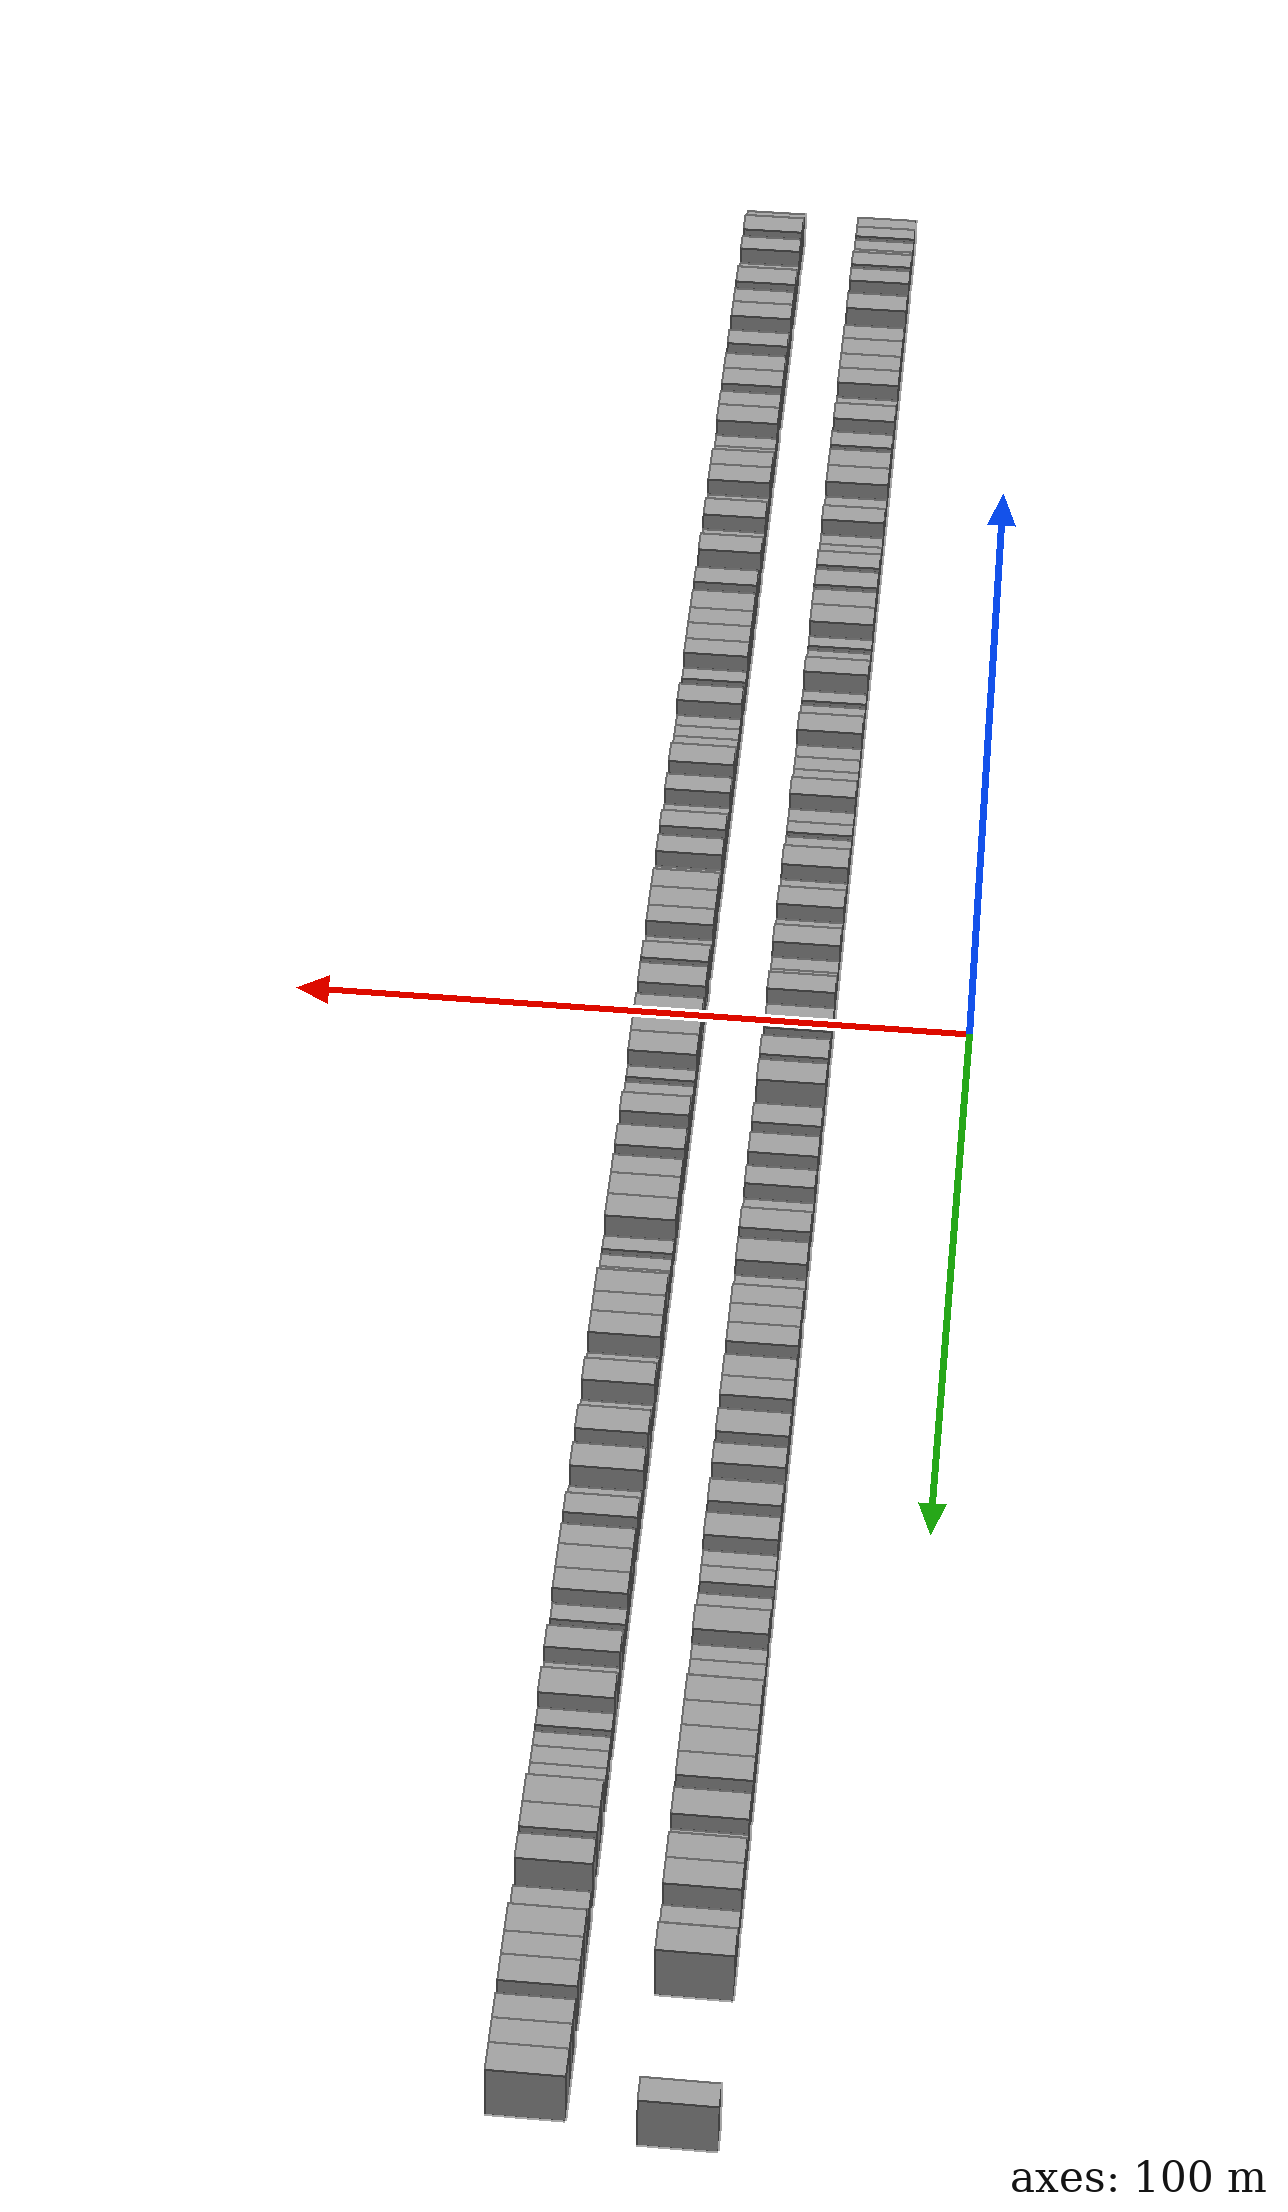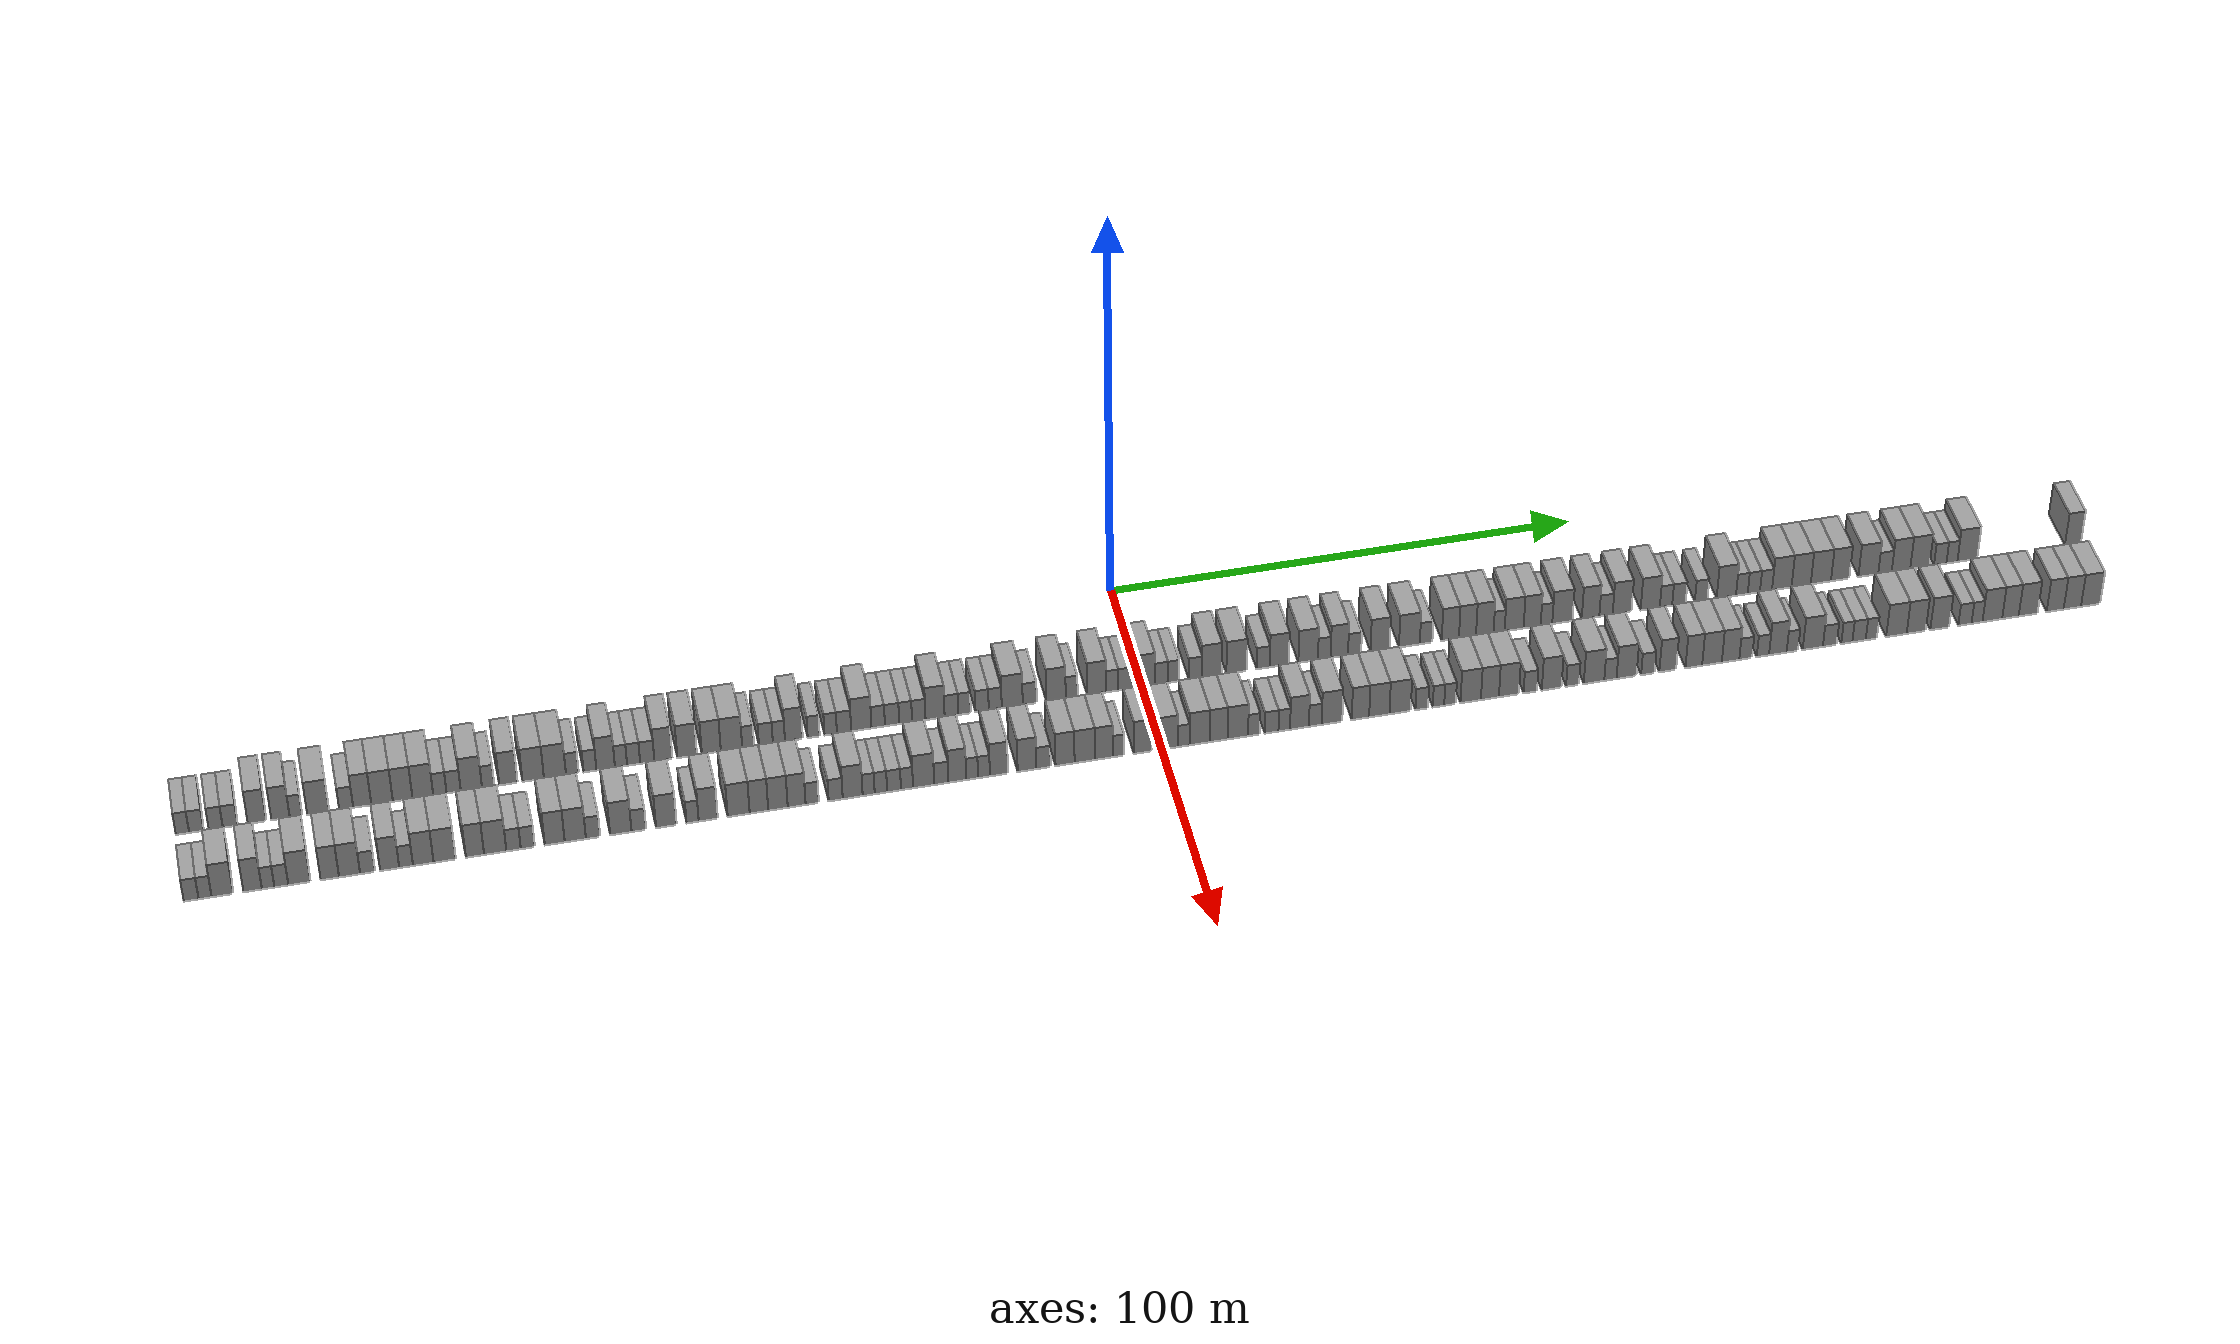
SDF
<sdf version="1.6">
 <world name="default">
  <scene>
   <sky><clouds><speed>12</speed></clouds></sky>
   <ambient>0.4 0.4 0.4 1</ambient>
   <background>0.7 0.7 0.7 1</background>
   <shadows>1</shadows>
  </scene>
  <gravity>0 0 -9.8066</gravity>
  <magnetic_field>6e-06 2.3e-05 -4.2e-05</magnetic_field>
  <physics default="0" name="default_physics" type="ode">
   <ode>
    <solver>
     <type>quick</type>
     <iters>10</iters>
     <sor>1.0</sor>
     <use_dynamic_moi_rescaling>0</use_dynamic_moi_rescaling>
    </solver>
    <constraints>
     <cfm>0</cfm>
     <erp>0.2</erp>
     <contact_max_correcting_vel>100</contact_max_correcting_vel>
     <contact_surface_layer>0.001</contact_surface_layer>
    </constraints>
   </ode>
   <max_step_size>0.004</max_step_size>
   <real_time_factor>1</real_time_factor>
   <real_time_update_rate>250</real_time_update_rate>
  </physics>
  <light name="sun" type="directional">
   <pose>0 0 10 0 0 0</pose>
   <diffuse>0.8 0.8 0.8 1</diffuse>
   <specular>0.2 0.2 0.2 1</specular>
   <attenuation>
    <range>1000</range>
    <constant>0.9</constant>
    <linear>0.01</linear>
    <quadratic>0.001</quadratic>
   </attenuation>
   <direction>-0.5 0.1 -0.9</direction>
  </light>
  <model name="building_1">
   <static>1</static>
   <pose>25.0000 -196.6714 0 0.000000 0.000000 0.000000</pose>
   <link name="link">
    <pose>0 0 3.00 0 0 0</pose>
    <collision name="collision"><geometry><box><size>10.0000 2.6572 6.0000</size></box></geometry></collision>
    <visual name="visual">
     <cast_shadows>0</cast_shadows>
     <geometry><box><size>10.0000 2.6572 6.0000</size></box></geometry>
     <material>
      <script>
       <uri>model://grey_wall/materials/scripts</uri>
       <uri>model://grey_wall/materials/textures</uri>
       <name>vrc/grey_wall</name>
      </script>
     </material>
    </visual>
   </link>
  </model>
  <model name="building_2">
   <static>1</static>
   <pose>25.0000 -193.8930 0 0.000000 0.000000 0.000000</pose>
   <link name="link">
    <pose>0 0 3.00 0 0 0</pose>
    <collision name="collision"><geometry><box><size>10.0000 2.8997 6.0000</size></box></geometry></collision>
    <visual name="visual">
     <cast_shadows>0</cast_shadows>
     <geometry><box><size>10.0000 2.8997 6.0000</size></box></geometry>
     <material>
      <script>
       <uri>model://grey_wall/materials/scripts</uri>
       <uri>model://grey_wall/materials/textures</uri>
       <name>vrc/grey_wall</name>
      </script>
     </material>
    </visual>
   </link>
  </model>
  <model name="building_3">
   <static>1</static>
   <pose>25.0000 -190.0357 0 0.000000 0.000000 0.000000</pose>
   <link name="link">
    <pose>0 0 3.00 0 0 0</pose>
    <collision name="collision"><geometry><box><size>10.0000 2.8149 6.0000</size></box></geometry></collision>
    <visual name="visual">
     <cast_shadows>0</cast_shadows>
     <geometry><box><size>10.0000 2.8149 6.0000</size></box></geometry>
     <material>
      <script>
       <uri>model://grey_wall/materials/scripts</uri>
       <uri>model://grey_wall/materials/textures</uri>
       <name>vrc/grey_wall</name>
      </script>
     </material>
    </visual>
   </link>
  </model>
  <model name="building_4">
   <static>1</static>
   <pose>25.0000 -187.1431 0 0.000000 0.000000 0.000000</pose>
   <link name="link">
    <pose>0 0 3.00 0 0 0</pose>
    <collision name="collision"><geometry><box><size>10.0000 2.9703 6.0000</size></box></geometry></collision>
    <visual name="visual">
     <cast_shadows>0</cast_shadows>
     <geometry><box><size>10.0000 2.9703 6.0000</size></box></geometry>
     <material>
      <script>
       <uri>model://grey_wall/materials/scripts</uri>
       <uri>model://grey_wall/materials/textures</uri>
       <name>vrc/grey_wall</name>
      </script>
     </material>
    </visual>
   </link>
  </model>
  <model name="building_5">
   <static>1</static>
   <pose>25.0000 -181.7959 0 0.000000 0.000000 0.000000</pose>
   <link name="link">
    <pose>0 0 4.50 0 0 0</pose>
    <collision name="collision"><geometry><box><size>10.0000 3.7241 9.0000</size></box></geometry></collision>
    <visual name="visual">
     <cast_shadows>0</cast_shadows>
     <geometry><box><size>10.0000 3.7241 9.0000</size></box></geometry>
     <material>
      <script>
       <uri>model://grey_wall/materials/scripts</uri>
       <uri>model://grey_wall/materials/textures</uri>
       <name>vrc/grey_wall</name>
      </script>
     </material>
    </visual>
   </link>
  </model>
  <model name="building_6">
   <static>1</static>
   <pose>25.0000 -177.0930 0 0.000000 0.000000 0.000000</pose>
   <link name="link">
    <pose>0 0 4.50 0 0 0</pose>
    <collision name="collision"><geometry><box><size>10.0000 3.6816 9.0000</size></box></geometry></collision>
    <visual name="visual">
     <cast_shadows>0</cast_shadows>
     <geometry><box><size>10.0000 3.6816 9.0000</size></box></geometry>
     <material>
      <script>
       <uri>model://grey_wall/materials/scripts</uri>
       <uri>model://grey_wall/materials/textures</uri>
       <name>vrc/grey_wall</name>
      </script>
     </material>
    </visual>
   </link>
  </model>
  <model name="building_7">
   <static>1</static>
   <pose>25.0000 -174.0085 0 0.000000 0.000000 0.000000</pose>
   <link name="link">
    <pose>0 0 3.00 0 0 0</pose>
    <collision name="collision"><geometry><box><size>10.0000 2.4874 6.0000</size></box></geometry></collision>
    <visual name="visual">
     <cast_shadows>0</cast_shadows>
     <geometry><box><size>10.0000 2.4874 6.0000</size></box></geometry>
     <material>
      <script>
       <uri>model://grey_wall/materials/scripts</uri>
       <uri>model://grey_wall/materials/textures</uri>
       <name>vrc/grey_wall</name>
      </script>
     </material>
    </visual>
   </link>
  </model>
  <model name="building_8">
   <static>1</static>
   <pose>25.0000 -169.5566 0 0.000000 0.000000 0.000000</pose>
   <link name="link">
    <pose>0 0 4.50 0 0 0</pose>
    <collision name="collision"><geometry><box><size>10.0000 4.4163 9.0000</size></box></geometry></collision>
    <visual name="visual">
     <cast_shadows>0</cast_shadows>
     <geometry><box><size>10.0000 4.4163 9.0000</size></box></geometry>
     <material>
      <script>
       <uri>model://grey_wall/materials/scripts</uri>
       <uri>model://grey_wall/materials/textures</uri>
       <name>vrc/grey_wall</name>
      </script>
     </material>
    </visual>
   </link>
  </model>
  <model name="building_9">
   <static>1</static>
   <pose>25.0000 -163.9405 0 0.000000 0.000000 0.000000</pose>
   <link name="link">
    <pose>0 0 3.00 0 0 0</pose>
    <collision name="collision"><geometry><box><size>10.0000 2.8160 6.0000</size></box></geometry></collision>
    <visual name="visual">
     <cast_shadows>0</cast_shadows>
     <geometry><box><size>10.0000 2.8160 6.0000</size></box></geometry>
     <material>
      <script>
       <uri>model://grey_wall/materials/scripts</uri>
       <uri>model://grey_wall/materials/textures</uri>
       <name>vrc/grey_wall</name>
      </script>
     </material>
    </visual>
   </link>
  </model>
  <model name="building_10">
   <static>1</static>
   <pose>25.0000 -160.7035 0 0.000000 0.000000 0.000000</pose>
   <link name="link">
    <pose>0 0 4.50 0 0 0</pose>
    <collision name="collision"><geometry><box><size>10.0000 3.6581 9.0000</size></box></geometry></collision>
    <visual name="visual">
     <cast_shadows>0</cast_shadows>
     <geometry><box><size>10.0000 3.6581 9.0000</size></box></geometry>
     <material>
      <script>
       <uri>model://grey_wall/materials/scripts</uri>
       <uri>model://grey_wall/materials/textures</uri>
       <name>vrc/grey_wall</name>
      </script>
     </material>
    </visual>
   </link>
  </model>
  <model name="building_11">
   <static>1</static>
   <pose>25.0000 -156.7026 0 0.000000 0.000000 0.000000</pose>
   <link name="link">
    <pose>0 0 4.50 0 0 0</pose>
    <collision name="collision"><geometry><box><size>10.0000 4.3437 9.0000</size></box></geometry></collision>
    <visual name="visual">
     <cast_shadows>0</cast_shadows>
     <geometry><box><size>10.0000 4.3437 9.0000</size></box></geometry>
     <material>
      <script>
       <uri>model://grey_wall/materials/scripts</uri>
       <uri>model://grey_wall/materials/textures</uri>
       <name>vrc/grey_wall</name>
      </script>
     </material>
    </visual>
   </link>
  </model>
  <model name="building_12">
   <static>1</static>
   <pose>25.0000 -152.5547 0 0.000000 0.000000 0.000000</pose>
   <link name="link">
    <pose>0 0 4.50 0 0 0</pose>
    <collision name="collision"><geometry><box><size>10.0000 3.9522 9.0000</size></box></geometry></collision>
    <visual name="visual">
     <cast_shadows>0</cast_shadows>
     <geometry><box><size>10.0000 3.9522 9.0000</size></box></geometry>
     <material>
      <script>
       <uri>model://grey_wall/materials/scripts</uri>
       <uri>model://grey_wall/materials/textures</uri>
       <name>vrc/grey_wall</name>
      </script>
     </material>
    </visual>
   </link>
  </model>
  <model name="building_13">
   <static>1</static>
   <pose>25.0000 -148.4807 0 0.000000 0.000000 0.000000</pose>
   <link name="link">
    <pose>0 0 4.50 0 0 0</pose>
    <collision name="collision"><geometry><box><size>10.0000 4.1957 9.0000</size></box></geometry></collision>
    <visual name="visual">
     <cast_shadows>0</cast_shadows>
     <geometry><box><size>10.0000 4.1957 9.0000</size></box></geometry>
     <material>
      <script>
       <uri>model://grey_wall/materials/scripts</uri>
       <uri>model://grey_wall/materials/textures</uri>
       <name>vrc/grey_wall</name>
      </script>
     </material>
    </visual>
   </link>
  </model>
  <model name="building_14">
   <static>1</static>
   <pose>25.0000 -145.0377 0 0.000000 0.000000 0.000000</pose>
   <link name="link">
    <pose>0 0 3.00 0 0 0</pose>
    <collision name="collision"><geometry><box><size>10.0000 2.6903 6.0000</size></box></geometry></collision>
    <visual name="visual">
     <cast_shadows>0</cast_shadows>
     <geometry><box><size>10.0000 2.6903 6.0000</size></box></geometry>
     <material>
      <script>
       <uri>model://grey_wall/materials/scripts</uri>
       <uri>model://grey_wall/materials/textures</uri>
       <name>vrc/grey_wall</name>
      </script>
     </material>
    </visual>
   </link>
  </model>
  <model name="building_15">
   <static>1</static>
   <pose>25.0000 -142.2592 0 0.000000 0.000000 0.000000</pose>
   <link name="link">
    <pose>0 0 3.00 0 0 0</pose>
    <collision name="collision"><geometry><box><size>10.0000 2.8667 6.0000</size></box></geometry></collision>
    <visual name="visual">
     <cast_shadows>0</cast_shadows>
     <geometry><box><size>10.0000 2.8667 6.0000</size></box></geometry>
     <material>
      <script>
       <uri>model://grey_wall/materials/scripts</uri>
       <uri>model://grey_wall/materials/textures</uri>
       <name>vrc/grey_wall</name>
      </script>
     </material>
    </visual>
   </link>
  </model>
  <model name="building_16">
   <static>1</static>
   <pose>25.0000 -138.6716 0 0.000000 0.000000 0.000000</pose>
   <link name="link">
    <pose>0 0 4.50 0 0 0</pose>
    <collision name="collision"><geometry><box><size>10.0000 4.3085 9.0000</size></box></geometry></collision>
    <visual name="visual">
     <cast_shadows>0</cast_shadows>
     <geometry><box><size>10.0000 4.3085 9.0000</size></box></geometry>
     <material>
      <script>
       <uri>model://grey_wall/materials/scripts</uri>
       <uri>model://grey_wall/materials/textures</uri>
       <name>vrc/grey_wall</name>
      </script>
     </material>
    </visual>
   </link>
  </model>
  <model name="building_17">
   <static>1</static>
   <pose>25.0000 -135.2732 0 0.000000 0.000000 0.000000</pose>
   <link name="link">
    <pose>0 0 3.00 0 0 0</pose>
    <collision name="collision"><geometry><box><size>10.0000 2.4883 6.0000</size></box></geometry></collision>
    <visual name="visual">
     <cast_shadows>0</cast_shadows>
     <geometry><box><size>10.0000 2.4883 6.0000</size></box></geometry>
     <material>
      <script>
       <uri>model://grey_wall/materials/scripts</uri>
       <uri>model://grey_wall/materials/textures</uri>
       <name>vrc/grey_wall</name>
      </script>
     </material>
    </visual>
   </link>
  </model>
  <model name="building_18">
   <static>1</static>
   <pose>25.0000 -131.1658 0 0.000000 0.000000 0.000000</pose>
   <link name="link">
    <pose>0 0 4.50 0 0 0</pose>
    <collision name="collision"><geometry><box><size>10.0000 3.7266 9.0000</size></box></geometry></collision>
    <visual name="visual">
     <cast_shadows>0</cast_shadows>
     <geometry><box><size>10.0000 3.7266 9.0000</size></box></geometry>
     <material>
      <script>
       <uri>model://grey_wall/materials/scripts</uri>
       <uri>model://grey_wall/materials/textures</uri>
       <name>vrc/grey_wall</name>
      </script>
     </material>
    </visual>
   </link>
  </model>
  <model name="building_19">
   <static>1</static>
   <pose>25.0000 -126.1264 0 0.000000 0.000000 0.000000</pose>
   <link name="link">
    <pose>0 0 4.50 0 0 0</pose>
    <collision name="collision"><geometry><box><size>10.0000 4.3522 9.0000</size></box></geometry></collision>
    <visual name="visual">
     <cast_shadows>0</cast_shadows>
     <geometry><box><size>10.0000 4.3522 9.0000</size></box></geometry>
     <material>
      <script>
       <uri>model://grey_wall/materials/scripts</uri>
       <uri>model://grey_wall/materials/textures</uri>
       <name>vrc/grey_wall</name>
      </script>
     </material>
    </visual>
   </link>
  </model>
  <model name="building_20">
   <static>1</static>
   <pose>25.0000 -121.7045 0 0.000000 0.000000 0.000000</pose>
   <link name="link">
    <pose>0 0 4.50 0 0 0</pose>
    <collision name="collision"><geometry><box><size>10.0000 4.4916 9.0000</size></box></geometry></collision>
    <visual name="visual">
     <cast_shadows>0</cast_shadows>
     <geometry><box><size>10.0000 4.4916 9.0000</size></box></geometry>
     <material>
      <script>
       <uri>model://grey_wall/materials/scripts</uri>
       <uri>model://grey_wall/materials/textures</uri>
       <name>vrc/grey_wall</name>
      </script>
     </material>
    </visual>
   </link>
  </model>
  <model name="building_21">
   <static>1</static>
   <pose>25.0000 -118.1646 0 0.000000 0.000000 0.000000</pose>
   <link name="link">
    <pose>0 0 3.00 0 0 0</pose>
    <collision name="collision"><geometry><box><size>10.0000 2.5880 6.0000</size></box></geometry></collision>
    <visual name="visual">
     <cast_shadows>0</cast_shadows>
     <geometry><box><size>10.0000 2.5880 6.0000</size></box></geometry>
     <material>
      <script>
       <uri>model://grey_wall/materials/scripts</uri>
       <uri>model://grey_wall/materials/textures</uri>
       <name>vrc/grey_wall</name>
      </script>
     </material>
    </visual>
   </link>
  </model>
  <model name="building_22">
   <static>1</static>
   <pose>25.0000 -114.5606 0 0.000000 0.000000 0.000000</pose>
   <link name="link">
    <pose>0 0 3.00 0 0 0</pose>
    <collision name="collision"><geometry><box><size>10.0000 2.6201 6.0000</size></box></geometry></collision>
    <visual name="visual">
     <cast_shadows>0</cast_shadows>
     <geometry><box><size>10.0000 2.6201 6.0000</size></box></geometry>
     <material>
      <script>
       <uri>model://grey_wall/materials/scripts</uri>
       <uri>model://grey_wall/materials/textures</uri>
       <name>vrc/grey_wall</name>
      </script>
     </material>
    </visual>
   </link>
  </model>
  <model name="building_23">
   <static>1</static>
   <pose>25.0000 -111.3578 0 0.000000 0.000000 0.000000</pose>
   <link name="link">
    <pose>0 0 4.50 0 0 0</pose>
    <collision name="collision"><geometry><box><size>10.0000 3.7856 9.0000</size></box></geometry></collision>
    <visual name="visual">
     <cast_shadows>0</cast_shadows>
     <geometry><box><size>10.0000 3.7856 9.0000</size></box></geometry>
     <material>
      <script>
       <uri>model://grey_wall/materials/scripts</uri>
       <uri>model://grey_wall/materials/textures</uri>
       <name>vrc/grey_wall</name>
      </script>
     </material>
    </visual>
   </link>
  </model>
  <model name="building_24">
   <static>1</static>
   <pose>25.0000 -108.2224 0 0.000000 0.000000 0.000000</pose>
   <link name="link">
    <pose>0 0 3.00 0 0 0</pose>
    <collision name="collision"><geometry><box><size>10.0000 2.4851 6.0000</size></box></geometry></collision>
    <visual name="visual">
     <cast_shadows>0</cast_shadows>
     <geometry><box><size>10.0000 2.4851 6.0000</size></box></geometry>
     <material>
      <script>
       <uri>model://grey_wall/materials/scripts</uri>
       <uri>model://grey_wall/materials/textures</uri>
       <name>vrc/grey_wall</name>
      </script>
     </material>
    </visual>
   </link>
  </model>
  <model name="building_25">
   <static>1</static>
   <pose>25.0000 -105.6417 0 0.000000 0.000000 0.000000</pose>
   <link name="link">
    <pose>0 0 3.00 0 0 0</pose>
    <collision name="collision"><geometry><box><size>10.0000 2.6763 6.0000</size></box></geometry></collision>
    <visual name="visual">
     <cast_shadows>0</cast_shadows>
     <geometry><box><size>10.0000 2.6763 6.0000</size></box></geometry>
     <material>
      <script>
       <uri>model://grey_wall/materials/scripts</uri>
       <uri>model://grey_wall/materials/textures</uri>
       <name>vrc/grey_wall</name>
      </script>
     </material>
    </visual>
   </link>
  </model>
  <model name="building_26">
   <static>1</static>
   <pose>25.0000 -102.8518 0 0.000000 0.000000 0.000000</pose>
   <link name="link">
    <pose>0 0 3.00 0 0 0</pose>
    <collision name="collision"><geometry><box><size>10.0000 2.9035 6.0000</size></box></geometry></collision>
    <visual name="visual">
     <cast_shadows>0</cast_shadows>
     <geometry><box><size>10.0000 2.9035 6.0000</size></box></geometry>
     <material>
      <script>
       <uri>model://grey_wall/materials/scripts</uri>
       <uri>model://grey_wall/materials/textures</uri>
       <name>vrc/grey_wall</name>
      </script>
     </material>
    </visual>
   </link>
  </model>
  <model name="building_27">
   <static>1</static>
   <pose>25.0000 -99.5508 0 0.000000 0.000000 0.000000</pose>
   <link name="link">
    <pose>0 0 4.50 0 0 0</pose>
    <collision name="collision"><geometry><box><size>10.0000 3.6984 9.0000</size></box></geometry></collision>
    <visual name="visual">
     <cast_shadows>0</cast_shadows>
     <geometry><box><size>10.0000 3.6984 9.0000</size></box></geometry>
     <material>
      <script>
       <uri>model://grey_wall/materials/scripts</uri>
       <uri>model://grey_wall/materials/textures</uri>
       <name>vrc/grey_wall</name>
      </script>
     </material>
    </visual>
   </link>
  </model>
  <model name="building_28">
   <static>1</static>
   <pose>25.0000 -94.6884 0 0.000000 0.000000 0.000000</pose>
   <link name="link">
    <pose>0 0 4.50 0 0 0</pose>
    <collision name="collision"><geometry><box><size>10.0000 4.0265 9.0000</size></box></geometry></collision>
    <visual name="visual">
     <cast_shadows>0</cast_shadows>
     <geometry><box><size>10.0000 4.0265 9.0000</size></box></geometry>
     <material>
      <script>
       <uri>model://grey_wall/materials/scripts</uri>
       <uri>model://grey_wall/materials/textures</uri>
       <name>vrc/grey_wall</name>
      </script>
     </material>
    </visual>
   </link>
  </model>
  <model name="building_29">
   <static>1</static>
   <pose>25.0000 -89.7209 0 0.000000 0.000000 0.000000</pose>
   <link name="link">
    <pose>0 0 4.50 0 0 0</pose>
    <collision name="collision"><geometry><box><size>10.0000 3.9085 9.0000</size></box></geometry></collision>
    <visual name="visual">
     <cast_shadows>0</cast_shadows>
     <geometry><box><size>10.0000 3.9085 9.0000</size></box></geometry>
     <material>
      <script>
       <uri>model://grey_wall/materials/scripts</uri>
       <uri>model://grey_wall/materials/textures</uri>
       <name>vrc/grey_wall</name>
      </script>
     </material>
    </visual>
   </link>
  </model>
  <model name="building_30">
   <static>1</static>
   <pose>25.0000 -85.5600 0 0.000000 0.000000 0.000000</pose>
   <link name="link">
    <pose>0 0 4.50 0 0 0</pose>
    <collision name="collision"><geometry><box><size>10.0000 4.4133 9.0000</size></box></geometry></collision>
    <visual name="visual">
     <cast_shadows>0</cast_shadows>
     <geometry><box><size>10.0000 4.4133 9.0000</size></box></geometry>
     <material>
      <script>
       <uri>model://grey_wall/materials/scripts</uri>
       <uri>model://grey_wall/materials/textures</uri>
       <name>vrc/grey_wall</name>
      </script>
     </material>
    </visual>
   </link>
  </model>
  <model name="building_31">
   <static>1</static>
   <pose>25.0000 -82.1395 0 0.000000 0.000000 0.000000</pose>
   <link name="link">
    <pose>0 0 3.00 0 0 0</pose>
    <collision name="collision"><geometry><box><size>10.0000 2.4278 6.0000</size></box></geometry></collision>
    <visual name="visual">
     <cast_shadows>0</cast_shadows>
     <geometry><box><size>10.0000 2.4278 6.0000</size></box></geometry>
     <material>
      <script>
       <uri>model://grey_wall/materials/scripts</uri>
       <uri>model://grey_wall/materials/textures</uri>
       <name>vrc/grey_wall</name>
      </script>
     </material>
    </visual>
   </link>
  </model>
  <model name="building_32">
   <static>1</static>
   <pose>25.0000 -78.4875 0 0.000000 0.000000 0.000000</pose>
   <link name="link">
    <pose>0 0 3.00 0 0 0</pose>
    <collision name="collision"><geometry><box><size>10.0000 2.8761 6.0000</size></box></geometry></collision>
    <visual name="visual">
     <cast_shadows>0</cast_shadows>
     <geometry><box><size>10.0000 2.8761 6.0000</size></box></geometry>
     <material>
      <script>
       <uri>model://grey_wall/materials/scripts</uri>
       <uri>model://grey_wall/materials/textures</uri>
       <name>vrc/grey_wall</name>
      </script>
     </material>
    </visual>
   </link>
  </model>
  <model name="building_33">
   <static>1</static>
   <pose>25.0000 -75.7986 0 0.000000 0.000000 0.000000</pose>
   <link name="link">
    <pose>0 0 3.00 0 0 0</pose>
    <collision name="collision"><geometry><box><size>10.0000 2.5016 6.0000</size></box></geometry></collision>
    <visual name="visual">
     <cast_shadows>0</cast_shadows>
     <geometry><box><size>10.0000 2.5016 6.0000</size></box></geometry>
     <material>
      <script>
       <uri>model://grey_wall/materials/scripts</uri>
       <uri>model://grey_wall/materials/textures</uri>
       <name>vrc/grey_wall</name>
      </script>
     </material>
    </visual>
   </link>
  </model>
  <model name="building_34">
   <static>1</static>
   <pose>25.0000 -72.7045 0 0.000000 0.000000 0.000000</pose>
   <link name="link">
    <pose>0 0 4.50 0 0 0</pose>
    <collision name="collision"><geometry><box><size>10.0000 3.6865 9.0000</size></box></geometry></collision>
    <visual name="visual">
     <cast_shadows>0</cast_shadows>
     <geometry><box><size>10.0000 3.6865 9.0000</size></box></geometry>
     <material>
      <script>
       <uri>model://grey_wall/materials/scripts</uri>
       <uri>model://grey_wall/materials/textures</uri>
       <name>vrc/grey_wall</name>
      </script>
     </material>
    </visual>
   </link>
  </model>
  <model name="building_35">
   <static>1</static>
   <pose>25.0000 -68.6142 0 0.000000 0.000000 0.000000</pose>
   <link name="link">
    <pose>0 0 3.00 0 0 0</pose>
    <collision name="collision"><geometry><box><size>10.0000 2.4942 6.0000</size></box></geometry></collision>
    <visual name="visual">
     <cast_shadows>0</cast_shadows>
     <geometry><box><size>10.0000 2.4942 6.0000</size></box></geometry>
     <material>
      <script>
       <uri>model://grey_wall/materials/scripts</uri>
       <uri>model://grey_wall/materials/textures</uri>
       <name>vrc/grey_wall</name>
      </script>
     </material>
    </visual>
   </link>
  </model>
  <model name="building_36">
   <static>1</static>
   <pose>25.0000 -65.0861 0 0.000000 0.000000 0.000000</pose>
   <link name="link">
    <pose>0 0 3.00 0 0 0</pose>
    <collision name="collision"><geometry><box><size>10.0000 2.5619 6.0000</size></box></geometry></collision>
    <visual name="visual">
     <cast_shadows>0</cast_shadows>
     <geometry><box><size>10.0000 2.5619 6.0000</size></box></geometry>
     <material>
      <script>
       <uri>model://grey_wall/materials/scripts</uri>
       <uri>model://grey_wall/materials/textures</uri>
       <name>vrc/grey_wall</name>
      </script>
     </material>
    </visual>
   </link>
  </model>
  <model name="building_37">
   <static>1</static>
   <pose>25.0000 -62.3235 0 0.000000 0.000000 0.000000</pose>
   <link name="link">
    <pose>0 0 3.00 0 0 0</pose>
    <collision name="collision"><geometry><box><size>10.0000 2.9633 6.0000</size></box></geometry></collision>
    <visual name="visual">
     <cast_shadows>0</cast_shadows>
     <geometry><box><size>10.0000 2.9633 6.0000</size></box></geometry>
     <material>
      <script>
       <uri>model://grey_wall/materials/scripts</uri>
       <uri>model://grey_wall/materials/textures</uri>
       <name>vrc/grey_wall</name>
      </script>
     </material>
    </visual>
   </link>
  </model>
  <model name="building_38">
   <static>1</static>
   <pose>25.0000 -58.7388 0 0.000000 0.000000 0.000000</pose>
   <link name="link">
    <pose>0 0 4.50 0 0 0</pose>
    <collision name="collision"><geometry><box><size>10.0000 4.2061 9.0000</size></box></geometry></collision>
    <visual name="visual">
     <cast_shadows>0</cast_shadows>
     <geometry><box><size>10.0000 4.2061 9.0000</size></box></geometry>
     <material>
      <script>
       <uri>model://grey_wall/materials/scripts</uri>
       <uri>model://grey_wall/materials/textures</uri>
       <name>vrc/grey_wall</name>
      </script>
     </material>
    </visual>
   </link>
  </model>
  <model name="building_39">
   <static>1</static>
   <pose>25.0000 -55.2406 0 0.000000 0.000000 0.000000</pose>
   <link name="link">
    <pose>0 0 3.00 0 0 0</pose>
    <collision name="collision"><geometry><box><size>10.0000 2.7902 6.0000</size></box></geometry></collision>
    <visual name="visual">
     <cast_shadows>0</cast_shadows>
     <geometry><box><size>10.0000 2.7902 6.0000</size></box></geometry>
     <material>
      <script>
       <uri>model://grey_wall/materials/scripts</uri>
       <uri>model://grey_wall/materials/textures</uri>
       <name>vrc/grey_wall</name>
      </script>
     </material>
    </visual>
   </link>
  </model>
  <model name="building_40">
   <static>1</static>
   <pose>25.0000 -52.3560 0 0.000000 0.000000 0.000000</pose>
   <link name="link">
    <pose>0 0 3.00 0 0 0</pose>
    <collision name="collision"><geometry><box><size>10.0000 2.9790 6.0000</size></box></geometry></collision>
    <visual name="visual">
     <cast_shadows>0</cast_shadows>
     <geometry><box><size>10.0000 2.9790 6.0000</size></box></geometry>
     <material>
      <script>
       <uri>model://grey_wall/materials/scripts</uri>
       <uri>model://grey_wall/materials/textures</uri>
       <name>vrc/grey_wall</name>
      </script>
     </material>
    </visual>
   </link>
  </model>
  <model name="building_41">
   <static>1</static>
   <pose>25.0000 -49.5357 0 0.000000 0.000000 0.000000</pose>
   <link name="link">
    <pose>0 0 3.00 0 0 0</pose>
    <collision name="collision"><geometry><box><size>10.0000 2.6617 6.0000</size></box></geometry></collision>
    <visual name="visual">
     <cast_shadows>0</cast_shadows>
     <geometry><box><size>10.0000 2.6617 6.0000</size></box></geometry>
     <material>
      <script>
       <uri>model://grey_wall/materials/scripts</uri>
       <uri>model://grey_wall/materials/textures</uri>
       <name>vrc/grey_wall</name>
      </script>
     </material>
    </visual>
   </link>
  </model>
  <model name="building_42">
   <static>1</static>
   <pose>25.0000 -46.8010 0 0.000000 0.000000 0.000000</pose>
   <link name="link">
    <pose>0 0 3.00 0 0 0</pose>
    <collision name="collision"><geometry><box><size>10.0000 2.8076 6.0000</size></box></geometry></collision>
    <visual name="visual">
     <cast_shadows>0</cast_shadows>
     <geometry><box><size>10.0000 2.8076 6.0000</size></box></geometry>
     <material>
      <script>
       <uri>model://grey_wall/materials/scripts</uri>
       <uri>model://grey_wall/materials/textures</uri>
       <name>vrc/grey_wall</name>
      </script>
     </material>
    </visual>
   </link>
  </model>
  <model name="building_43">
   <static>1</static>
   <pose>25.0000 -43.4065 0 0.000000 0.000000 0.000000</pose>
   <link name="link">
    <pose>0 0 4.50 0 0 0</pose>
    <collision name="collision"><geometry><box><size>10.0000 3.9816 9.0000</size></box></geometry></collision>
    <visual name="visual">
     <cast_shadows>0</cast_shadows>
     <geometry><box><size>10.0000 3.9816 9.0000</size></box></geometry>
     <material>
      <script>
       <uri>model://grey_wall/materials/scripts</uri>
       <uri>model://grey_wall/materials/textures</uri>
       <name>vrc/grey_wall</name>
      </script>
     </material>
    </visual>
   </link>
  </model>
  <model name="building_44">
   <static>1</static>
   <pose>25.0000 -39.9790 0 0.000000 0.000000 0.000000</pose>
   <link name="link">
    <pose>0 0 3.00 0 0 0</pose>
    <collision name="collision"><geometry><box><size>10.0000 2.8733 6.0000</size></box></geometry></collision>
    <visual name="visual">
     <cast_shadows>0</cast_shadows>
     <geometry><box><size>10.0000 2.8733 6.0000</size></box></geometry>
     <material>
      <script>
       <uri>model://grey_wall/materials/scripts</uri>
       <uri>model://grey_wall/materials/textures</uri>
       <name>vrc/grey_wall</name>
      </script>
     </material>
    </visual>
   </link>
  </model>
  <model name="building_45">
   <static>1</static>
   <pose>25.0000 -37.2530 0 0.000000 0.000000 0.000000</pose>
   <link name="link">
    <pose>0 0 3.00 0 0 0</pose>
    <collision name="collision"><geometry><box><size>10.0000 2.5789 6.0000</size></box></geometry></collision>
    <visual name="visual">
     <cast_shadows>0</cast_shadows>
     <geometry><box><size>10.0000 2.5789 6.0000</size></box></geometry>
     <material>
      <script>
       <uri>model://grey_wall/materials/scripts</uri>
       <uri>model://grey_wall/materials/textures</uri>
       <name>vrc/grey_wall</name>
      </script>
     </material>
    </visual>
   </link>
  </model>
  <model name="building_46">
   <static>1</static>
   <pose>25.0000 -33.5824 0 0.000000 0.000000 0.000000</pose>
   <link name="link">
    <pose>0 0 3.00 0 0 0</pose>
    <collision name="collision"><geometry><box><size>10.0000 2.7622 6.0000</size></box></geometry></collision>
    <visual name="visual">
     <cast_shadows>0</cast_shadows>
     <geometry><box><size>10.0000 2.7622 6.0000</size></box></geometry>
     <material>
      <script>
       <uri>model://grey_wall/materials/scripts</uri>
       <uri>model://grey_wall/materials/textures</uri>
       <name>vrc/grey_wall</name>
      </script>
     </material>
    </visual>
   </link>
  </model>
  <model name="building_47">
   <static>1</static>
   <pose>25.0000 -30.8432 0 0.000000 0.000000 0.000000</pose>
   <link name="link">
    <pose>0 0 3.00 0 0 0</pose>
    <collision name="collision"><geometry><box><size>10.0000 2.7163 6.0000</size></box></geometry></collision>
    <visual name="visual">
     <cast_shadows>0</cast_shadows>
     <geometry><box><size>10.0000 2.7163 6.0000</size></box></geometry>
     <material>
      <script>
       <uri>model://grey_wall/materials/scripts</uri>
       <uri>model://grey_wall/materials/textures</uri>
       <name>vrc/grey_wall</name>
      </script>
     </material>
    </visual>
   </link>
  </model>
  <model name="building_48">
   <static>1</static>
   <pose>25.0000 -27.2847 0 0.000000 0.000000 0.000000</pose>
   <link name="link">
    <pose>0 0 4.50 0 0 0</pose>
    <collision name="collision"><geometry><box><size>10.0000 4.4005 9.0000</size></box></geometry></collision>
    <visual name="visual">
     <cast_shadows>0</cast_shadows>
     <geometry><box><size>10.0000 4.4005 9.0000</size></box></geometry>
     <material>
      <script>
       <uri>model://grey_wall/materials/scripts</uri>
       <uri>model://grey_wall/materials/textures</uri>
       <name>vrc/grey_wall</name>
      </script>
     </material>
    </visual>
   </link>
  </model>
  <model name="building_49">
   <static>1</static>
   <pose>25.0000 -23.6133 0 0.000000 0.000000 0.000000</pose>
   <link name="link">
    <pose>0 0 3.00 0 0 0</pose>
    <collision name="collision"><geometry><box><size>10.0000 2.9424 6.0000</size></box></geometry></collision>
    <visual name="visual">
     <cast_shadows>0</cast_shadows>
     <geometry><box><size>10.0000 2.9424 6.0000</size></box></geometry>
     <material>
      <script>
       <uri>model://grey_wall/materials/scripts</uri>
       <uri>model://grey_wall/materials/textures</uri>
       <name>vrc/grey_wall</name>
      </script>
     </material>
    </visual>
   </link>
  </model>
  <model name="building_50">
   <static>1</static>
   <pose>25.0000 -18.1040 0 0.000000 0.000000 0.000000</pose>
   <link name="link">
    <pose>0 0 4.50 0 0 0</pose>
    <collision name="collision"><geometry><box><size>10.0000 4.0762 9.0000</size></box></geometry></collision>
    <visual name="visual">
     <cast_shadows>0</cast_shadows>
     <geometry><box><size>10.0000 4.0762 9.0000</size></box></geometry>
     <material>
      <script>
       <uri>model://grey_wall/materials/scripts</uri>
       <uri>model://grey_wall/materials/textures</uri>
       <name>vrc/grey_wall</name>
      </script>
     </material>
    </visual>
   </link>
  </model>
  <model name="building_51">
   <static>1</static>
   <pose>25.0000 -14.8109 0 0.000000 0.000000 0.000000</pose>
   <link name="link">
    <pose>0 0 3.00 0 0 0</pose>
    <collision name="collision"><geometry><box><size>10.0000 2.5101 6.0000</size></box></geometry></collision>
    <visual name="visual">
     <cast_shadows>0</cast_shadows>
     <geometry><box><size>10.0000 2.5101 6.0000</size></box></geometry>
     <material>
      <script>
       <uri>model://grey_wall/materials/scripts</uri>
       <uri>model://grey_wall/materials/textures</uri>
       <name>vrc/grey_wall</name>
      </script>
     </material>
    </visual>
   </link>
  </model>
  <model name="building_52">
   <static>1</static>
   <pose>25.0000 -9.5734 0 0.000000 0.000000 0.000000</pose>
   <link name="link">
    <pose>0 0 4.50 0 0 0</pose>
    <collision name="collision"><geometry><box><size>10.0000 3.9649 9.0000</size></box></geometry></collision>
    <visual name="visual">
     <cast_shadows>0</cast_shadows>
     <geometry><box><size>10.0000 3.9649 9.0000</size></box></geometry>
     <material>
      <script>
       <uri>model://grey_wall/materials/scripts</uri>
       <uri>model://grey_wall/materials/textures</uri>
       <name>vrc/grey_wall</name>
      </script>
     </material>
    </visual>
   </link>
  </model>
  <model name="building_53">
   <static>1</static>
   <pose>25.0000 -6.2797 0 0.000000 0.000000 0.000000</pose>
   <link name="link">
    <pose>0 0 3.00 0 0 0</pose>
    <collision name="collision"><geometry><box><size>10.0000 2.6224 6.0000</size></box></geometry></collision>
    <visual name="visual">
     <cast_shadows>0</cast_shadows>
     <geometry><box><size>10.0000 2.6224 6.0000</size></box></geometry>
     <material>
      <script>
       <uri>model://grey_wall/materials/scripts</uri>
       <uri>model://grey_wall/materials/textures</uri>
       <name>vrc/grey_wall</name>
      </script>
     </material>
    </visual>
   </link>
  </model>
  <model name="building_54">
   <static>1</static>
   <pose>25.0000 -3.4822 0 0.000000 0.000000 0.000000</pose>
   <link name="link">
    <pose>0 0 3.00 0 0 0</pose>
    <collision name="collision"><geometry><box><size>10.0000 2.9726 6.0000</size></box></geometry></collision>
    <visual name="visual">
     <cast_shadows>0</cast_shadows>
     <geometry><box><size>10.0000 2.9726 6.0000</size></box></geometry>
     <material>
      <script>
       <uri>model://grey_wall/materials/scripts</uri>
       <uri>model://grey_wall/materials/textures</uri>
       <name>vrc/grey_wall</name>
      </script>
     </material>
    </visual>
   </link>
  </model>
  <model name="building_55">
   <static>1</static>
   <pose>25.0000 0.8563 0 0.000000 0.000000 0.000000</pose>
   <link name="link">
    <pose>0 0 4.50 0 0 0</pose>
    <collision name="collision"><geometry><box><size>10.0000 3.7045 9.0000</size></box></geometry></collision>
    <visual name="visual">
     <cast_shadows>0</cast_shadows>
     <geometry><box><size>10.0000 3.7045 9.0000</size></box></geometry>
     <material>
      <script>
       <uri>model://grey_wall/materials/scripts</uri>
       <uri>model://grey_wall/materials/textures</uri>
       <name>vrc/grey_wall</name>
      </script>
     </material>
    </visual>
   </link>
  </model>
  <model name="building_56">
   <static>1</static>
   <pose>25.0000 4.0962 0 0.000000 0.000000 0.000000</pose>
   <link name="link">
    <pose>0 0 3.00 0 0 0</pose>
    <collision name="collision"><geometry><box><size>10.0000 2.7753 6.0000</size></box></geometry></collision>
    <visual name="visual">
     <cast_shadows>0</cast_shadows>
     <geometry><box><size>10.0000 2.7753 6.0000</size></box></geometry>
     <material>
      <script>
       <uri>model://grey_wall/materials/scripts</uri>
       <uri>model://grey_wall/materials/textures</uri>
       <name>vrc/grey_wall</name>
      </script>
     </material>
    </visual>
   </link>
  </model>
  <model name="building_57">
   <static>1</static>
   <pose>25.0000 6.6887 0 0.000000 0.000000 0.000000</pose>
   <link name="link">
    <pose>0 0 3.00 0 0 0</pose>
    <collision name="collision"><geometry><box><size>10.0000 2.4099 6.0000</size></box></geometry></collision>
    <visual name="visual">
     <cast_shadows>0</cast_shadows>
     <geometry><box><size>10.0000 2.4099 6.0000</size></box></geometry>
     <material>
      <script>
       <uri>model://grey_wall/materials/scripts</uri>
       <uri>model://grey_wall/materials/textures</uri>
       <name>vrc/grey_wall</name>
      </script>
     </material>
    </visual>
   </link>
  </model>
  <model name="building_58">
   <static>1</static>
   <pose>25.0000 11.3192 0 0.000000 0.000000 0.000000</pose>
   <link name="link">
    <pose>0 0 3.00 0 0 0</pose>
    <collision name="collision"><geometry><box><size>10.0000 2.8510 6.0000</size></box></geometry></collision>
    <visual name="visual">
     <cast_shadows>0</cast_shadows>
     <geometry><box><size>10.0000 2.8510 6.0000</size></box></geometry>
     <material>
      <script>
       <uri>model://grey_wall/materials/scripts</uri>
       <uri>model://grey_wall/materials/textures</uri>
       <name>vrc/grey_wall</name>
      </script>
     </material>
    </visual>
   </link>
  </model>
  <model name="building_59">
   <static>1</static>
   <pose>25.0000 14.8123 0 0.000000 0.000000 0.000000</pose>
   <link name="link">
    <pose>0 0 4.50 0 0 0</pose>
    <collision name="collision"><geometry><box><size>10.0000 4.1352 9.0000</size></box></geometry></collision>
    <visual name="visual">
     <cast_shadows>0</cast_shadows>
     <geometry><box><size>10.0000 4.1352 9.0000</size></box></geometry>
     <material>
      <script>
       <uri>model://grey_wall/materials/scripts</uri>
       <uri>model://grey_wall/materials/textures</uri>
       <name>vrc/grey_wall</name>
      </script>
     </material>
    </visual>
   </link>
  </model>
  <model name="building_60">
   <static>1</static>
   <pose>25.0000 20.0872 0 0.000000 0.000000 0.000000</pose>
   <link name="link">
    <pose>0 0 4.50 0 0 0</pose>
    <collision name="collision"><geometry><box><size>10.0000 4.4147 9.0000</size></box></geometry></collision>
    <visual name="visual">
     <cast_shadows>0</cast_shadows>
     <geometry><box><size>10.0000 4.4147 9.0000</size></box></geometry>
     <material>
      <script>
       <uri>model://grey_wall/materials/scripts</uri>
       <uri>model://grey_wall/materials/textures</uri>
       <name>vrc/grey_wall</name>
      </script>
     </material>
    </visual>
   </link>
  </model>
  <model name="building_61">
   <static>1</static>
   <pose>25.0000 25.7175 0 0.000000 0.000000 0.000000</pose>
   <link name="link">
    <pose>0 0 3.00 0 0 0</pose>
    <collision name="collision"><geometry><box><size>10.0000 2.8458 6.0000</size></box></geometry></collision>
    <visual name="visual">
     <cast_shadows>0</cast_shadows>
     <geometry><box><size>10.0000 2.8458 6.0000</size></box></geometry>
     <material>
      <script>
       <uri>model://grey_wall/materials/scripts</uri>
       <uri>model://grey_wall/materials/textures</uri>
       <name>vrc/grey_wall</name>
      </script>
     </material>
    </visual>
   </link>
  </model>
  <model name="building_62">
   <static>1</static>
   <pose>25.0000 29.1685 0 0.000000 0.000000 0.000000</pose>
   <link name="link">
    <pose>0 0 4.50 0 0 0</pose>
    <collision name="collision"><geometry><box><size>10.0000 4.0562 9.0000</size></box></geometry></collision>
    <visual name="visual">
     <cast_shadows>0</cast_shadows>
     <geometry><box><size>10.0000 4.0562 9.0000</size></box></geometry>
     <material>
      <script>
       <uri>model://grey_wall/materials/scripts</uri>
       <uri>model://grey_wall/materials/textures</uri>
       <name>vrc/grey_wall</name>
      </script>
     </material>
    </visual>
   </link>
  </model>
  <model name="building_63">
   <static>1</static>
   <pose>25.0000 35.2940 0 0.000000 0.000000 0.000000</pose>
   <link name="link">
    <pose>0 0 4.50 0 0 0</pose>
    <collision name="collision"><geometry><box><size>10.0000 4.1949 9.0000</size></box></geometry></collision>
    <visual name="visual">
     <cast_shadows>0</cast_shadows>
     <geometry><box><size>10.0000 4.1949 9.0000</size></box></geometry>
     <material>
      <script>
       <uri>model://grey_wall/materials/scripts</uri>
       <uri>model://grey_wall/materials/textures</uri>
       <name>vrc/grey_wall</name>
      </script>
     </material>
    </visual>
   </link>
  </model>
  <model name="building_64">
   <static>1</static>
   <pose>25.0000 38.7479 0 0.000000 0.000000 0.000000</pose>
   <link name="link">
    <pose>0 0 3.00 0 0 0</pose>
    <collision name="collision"><geometry><box><size>10.0000 2.7130 6.0000</size></box></geometry></collision>
    <visual name="visual">
     <cast_shadows>0</cast_shadows>
     <geometry><box><size>10.0000 2.7130 6.0000</size></box></geometry>
     <material>
      <script>
       <uri>model://grey_wall/materials/scripts</uri>
       <uri>model://grey_wall/materials/textures</uri>
       <name>vrc/grey_wall</name>
      </script>
     </material>
    </visual>
   </link>
  </model>
  <model name="building_65">
   <static>1</static>
   <pose>25.0000 41.9593 0 0.000000 0.000000 0.000000</pose>
   <link name="link">
    <pose>0 0 4.50 0 0 0</pose>
    <collision name="collision"><geometry><box><size>10.0000 3.7097 9.0000</size></box></geometry></collision>
    <visual name="visual">
     <cast_shadows>0</cast_shadows>
     <geometry><box><size>10.0000 3.7097 9.0000</size></box></geometry>
     <material>
      <script>
       <uri>model://grey_wall/materials/scripts</uri>
       <uri>model://grey_wall/materials/textures</uri>
       <name>vrc/grey_wall</name>
      </script>
     </material>
    </visual>
   </link>
  </model>
  <model name="building_66">
   <static>1</static>
   <pose>25.0000 45.2217 0 0.000000 0.000000 0.000000</pose>
   <link name="link">
    <pose>0 0 3.00 0 0 0</pose>
    <collision name="collision"><geometry><box><size>10.0000 2.8151 6.0000</size></box></geometry></collision>
    <visual name="visual">
     <cast_shadows>0</cast_shadows>
     <geometry><box><size>10.0000 2.8151 6.0000</size></box></geometry>
     <material>
      <script>
       <uri>model://grey_wall/materials/scripts</uri>
       <uri>model://grey_wall/materials/textures</uri>
       <name>vrc/grey_wall</name>
      </script>
     </material>
    </visual>
   </link>
  </model>
  <model name="building_67">
   <static>1</static>
   <pose>25.0000 50.6788 0 0.000000 0.000000 0.000000</pose>
   <link name="link">
    <pose>0 0 4.50 0 0 0</pose>
    <collision name="collision"><geometry><box><size>10.0000 4.0991 9.0000</size></box></geometry></collision>
    <visual name="visual">
     <cast_shadows>0</cast_shadows>
     <geometry><box><size>10.0000 4.0991 9.0000</size></box></geometry>
     <material>
      <script>
       <uri>model://grey_wall/materials/scripts</uri>
       <uri>model://grey_wall/materials/textures</uri>
       <name>vrc/grey_wall</name>
      </script>
     </material>
    </visual>
   </link>
  </model>
  <model name="building_68">
   <static>1</static>
   <pose>25.0000 56.9663 0 0.000000 0.000000 0.000000</pose>
   <link name="link">
    <pose>0 0 4.50 0 0 0</pose>
    <collision name="collision"><geometry><box><size>10.0000 4.4758 9.0000</size></box></geometry></collision>
    <visual name="visual">
     <cast_shadows>0</cast_shadows>
     <geometry><box><size>10.0000 4.4758 9.0000</size></box></geometry>
     <material>
      <script>
       <uri>model://grey_wall/materials/scripts</uri>
       <uri>model://grey_wall/materials/textures</uri>
       <name>vrc/grey_wall</name>
      </script>
     </material>
    </visual>
   </link>
  </model>
  <model name="building_69">
   <static>1</static>
   <pose>25.0000 60.5563 0 0.000000 0.000000 0.000000</pose>
   <link name="link">
    <pose>0 0 3.00 0 0 0</pose>
    <collision name="collision"><geometry><box><size>10.0000 2.7041 6.0000</size></box></geometry></collision>
    <visual name="visual">
     <cast_shadows>0</cast_shadows>
     <geometry><box><size>10.0000 2.7041 6.0000</size></box></geometry>
     <material>
      <script>
       <uri>model://grey_wall/materials/scripts</uri>
       <uri>model://grey_wall/materials/textures</uri>
       <name>vrc/grey_wall</name>
      </script>
     </material>
    </visual>
   </link>
  </model>
  <model name="building_70">
   <static>1</static>
   <pose>25.0000 65.7661 0 0.000000 0.000000 0.000000</pose>
   <link name="link">
    <pose>0 0 4.50 0 0 0</pose>
    <collision name="collision"><geometry><box><size>10.0000 3.7156 9.0000</size></box></geometry></collision>
    <visual name="visual">
     <cast_shadows>0</cast_shadows>
     <geometry><box><size>10.0000 3.7156 9.0000</size></box></geometry>
     <material>
      <script>
       <uri>model://grey_wall/materials/scripts</uri>
       <uri>model://grey_wall/materials/textures</uri>
       <name>vrc/grey_wall</name>
      </script>
     </material>
    </visual>
   </link>
  </model>
  <model name="building_71">
   <static>1</static>
   <pose>25.0000 69.4646 0 0.000000 0.000000 0.000000</pose>
   <link name="link">
    <pose>0 0 4.50 0 0 0</pose>
    <collision name="collision"><geometry><box><size>10.0000 3.6813 9.0000</size></box></geometry></collision>
    <visual name="visual">
     <cast_shadows>0</cast_shadows>
     <geometry><box><size>10.0000 3.6813 9.0000</size></box></geometry>
     <material>
      <script>
       <uri>model://grey_wall/materials/scripts</uri>
       <uri>model://grey_wall/materials/textures</uri>
       <name>vrc/grey_wall</name>
      </script>
     </material>
    </visual>
   </link>
  </model>
  <model name="building_72">
   <static>1</static>
   <pose>25.0000 73.1962 0 0.000000 0.000000 0.000000</pose>
   <link name="link">
    <pose>0 0 4.50 0 0 0</pose>
    <collision name="collision"><geometry><box><size>10.0000 3.7819 9.0000</size></box></geometry></collision>
    <visual name="visual">
     <cast_shadows>0</cast_shadows>
     <geometry><box><size>10.0000 3.7819 9.0000</size></box></geometry>
     <material>
      <script>
       <uri>model://grey_wall/materials/scripts</uri>
       <uri>model://grey_wall/materials/textures</uri>
       <name>vrc/grey_wall</name>
      </script>
     </material>
    </visual>
   </link>
  </model>
  <model name="building_73">
   <static>1</static>
   <pose>25.0000 76.2872 0 0.000000 0.000000 0.000000</pose>
   <link name="link">
    <pose>0 0 3.00 0 0 0</pose>
    <collision name="collision"><geometry><box><size>10.0000 2.4002 6.0000</size></box></geometry></collision>
    <visual name="visual">
     <cast_shadows>0</cast_shadows>
     <geometry><box><size>10.0000 2.4002 6.0000</size></box></geometry>
     <material>
      <script>
       <uri>model://grey_wall/materials/scripts</uri>
       <uri>model://grey_wall/materials/textures</uri>
       <name>vrc/grey_wall</name>
      </script>
     </material>
    </visual>
   </link>
  </model>
  <model name="building_74">
   <static>1</static>
   <pose>25.0000 79.5328 0 0.000000 0.000000 0.000000</pose>
   <link name="link">
    <pose>0 0 4.50 0 0 0</pose>
    <collision name="collision"><geometry><box><size>10.0000 4.0908 9.0000</size></box></geometry></collision>
    <visual name="visual">
     <cast_shadows>0</cast_shadows>
     <geometry><box><size>10.0000 4.0908 9.0000</size></box></geometry>
     <material>
      <script>
       <uri>model://grey_wall/materials/scripts</uri>
       <uri>model://grey_wall/materials/textures</uri>
       <name>vrc/grey_wall</name>
      </script>
     </material>
    </visual>
   </link>
  </model>
  <model name="building_75">
   <static>1</static>
   <pose>25.0000 83.4289 0 0.000000 0.000000 0.000000</pose>
   <link name="link">
    <pose>0 0 4.50 0 0 0</pose>
    <collision name="collision"><geometry><box><size>10.0000 3.7014 9.0000</size></box></geometry></collision>
    <visual name="visual">
     <cast_shadows>0</cast_shadows>
     <geometry><box><size>10.0000 3.7014 9.0000</size></box></geometry>
     <material>
      <script>
       <uri>model://grey_wall/materials/scripts</uri>
       <uri>model://grey_wall/materials/textures</uri>
       <name>vrc/grey_wall</name>
      </script>
     </material>
    </visual>
   </link>
  </model>
  <model name="building_76">
   <static>1</static>
   <pose>25.0000 86.5332 0 0.000000 0.000000 0.000000</pose>
   <link name="link">
    <pose>0 0 3.00 0 0 0</pose>
    <collision name="collision"><geometry><box><size>10.0000 2.5073 6.0000</size></box></geometry></collision>
    <visual name="visual">
     <cast_shadows>0</cast_shadows>
     <geometry><box><size>10.0000 2.5073 6.0000</size></box></geometry>
     <material>
      <script>
       <uri>model://grey_wall/materials/scripts</uri>
       <uri>model://grey_wall/materials/textures</uri>
       <name>vrc/grey_wall</name>
      </script>
     </material>
    </visual>
   </link>
  </model>
  <model name="building_77">
   <static>1</static>
   <pose>25.0000 89.9837 0 0.000000 0.000000 0.000000</pose>
   <link name="link">
    <pose>0 0 4.50 0 0 0</pose>
    <collision name="collision"><geometry><box><size>10.0000 4.3937 9.0000</size></box></geometry></collision>
    <visual name="visual">
     <cast_shadows>0</cast_shadows>
     <geometry><box><size>10.0000 4.3937 9.0000</size></box></geometry>
     <material>
      <script>
       <uri>model://grey_wall/materials/scripts</uri>
       <uri>model://grey_wall/materials/textures</uri>
       <name>vrc/grey_wall</name>
      </script>
     </material>
    </visual>
   </link>
  </model>
  <model name="building_78">
   <static>1</static>
   <pose>25.0000 96.0907 0 0.000000 0.000000 0.000000</pose>
   <link name="link">
    <pose>0 0 4.50 0 0 0</pose>
    <collision name="collision"><geometry><box><size>10.0000 3.8204 9.0000</size></box></geometry></collision>
    <visual name="visual">
     <cast_shadows>0</cast_shadows>
     <geometry><box><size>10.0000 3.8204 9.0000</size></box></geometry>
     <material>
      <script>
       <uri>model://grey_wall/materials/scripts</uri>
       <uri>model://grey_wall/materials/textures</uri>
       <name>vrc/grey_wall</name>
      </script>
     </material>
    </visual>
   </link>
  </model>
  <model name="building_79">
   <static>1</static>
   <pose>25.0000 99.4555 0 0.000000 0.000000 0.000000</pose>
   <link name="link">
    <pose>0 0 3.00 0 0 0</pose>
    <collision name="collision"><geometry><box><size>10.0000 2.9091 6.0000</size></box></geometry></collision>
    <visual name="visual">
     <cast_shadows>0</cast_shadows>
     <geometry><box><size>10.0000 2.9091 6.0000</size></box></geometry>
     <material>
      <script>
       <uri>model://grey_wall/materials/scripts</uri>
       <uri>model://grey_wall/materials/textures</uri>
       <name>vrc/grey_wall</name>
      </script>
     </material>
    </visual>
   </link>
  </model>
  <model name="building_80">
   <static>1</static>
   <pose>25.0000 102.9547 0 0.000000 0.000000 0.000000</pose>
   <link name="link">
    <pose>0 0 4.50 0 0 0</pose>
    <collision name="collision"><geometry><box><size>10.0000 4.0892 9.0000</size></box></geometry></collision>
    <visual name="visual">
     <cast_shadows>0</cast_shadows>
     <geometry><box><size>10.0000 4.0892 9.0000</size></box></geometry>
     <material>
      <script>
       <uri>model://grey_wall/materials/scripts</uri>
       <uri>model://grey_wall/materials/textures</uri>
       <name>vrc/grey_wall</name>
      </script>
     </material>
    </visual>
   </link>
  </model>
  <model name="building_81">
   <static>1</static>
   <pose>25.0000 109.0985 0 0.000000 0.000000 0.000000</pose>
   <link name="link">
    <pose>0 0 4.50 0 0 0</pose>
    <collision name="collision"><geometry><box><size>10.0000 4.1983 9.0000</size></box></geometry></collision>
    <visual name="visual">
     <cast_shadows>0</cast_shadows>
     <geometry><box><size>10.0000 4.1983 9.0000</size></box></geometry>
     <material>
      <script>
       <uri>model://grey_wall/materials/scripts</uri>
       <uri>model://grey_wall/materials/textures</uri>
       <name>vrc/grey_wall</name>
      </script>
     </material>
    </visual>
   </link>
  </model>
  <model name="building_82">
   <static>1</static>
   <pose>25.0000 112.5447 0 0.000000 0.000000 0.000000</pose>
   <link name="link">
    <pose>0 0 3.00 0 0 0</pose>
    <collision name="collision"><geometry><box><size>10.0000 2.6942 6.0000</size></box></geometry></collision>
    <visual name="visual">
     <cast_shadows>0</cast_shadows>
     <geometry><box><size>10.0000 2.6942 6.0000</size></box></geometry>
     <material>
      <script>
       <uri>model://grey_wall/materials/scripts</uri>
       <uri>model://grey_wall/materials/textures</uri>
       <name>vrc/grey_wall</name>
      </script>
     </material>
    </visual>
   </link>
  </model>
  <model name="building_83">
   <static>1</static>
   <pose>25.0000 115.3727 0 0.000000 0.000000 0.000000</pose>
   <link name="link">
    <pose>0 0 3.00 0 0 0</pose>
    <collision name="collision"><geometry><box><size>10.0000 2.9618 6.0000</size></box></geometry></collision>
    <visual name="visual">
     <cast_shadows>0</cast_shadows>
     <geometry><box><size>10.0000 2.9618 6.0000</size></box></geometry>
     <material>
      <script>
       <uri>model://grey_wall/materials/scripts</uri>
       <uri>model://grey_wall/materials/textures</uri>
       <name>vrc/grey_wall</name>
      </script>
     </material>
    </visual>
   </link>
  </model>
  <model name="building_84">
   <static>1</static>
   <pose>25.0000 120.2411 0 0.000000 0.000000 0.000000</pose>
   <link name="link">
    <pose>0 0 3.00 0 0 0</pose>
    <collision name="collision"><geometry><box><size>10.0000 2.7749 6.0000</size></box></geometry></collision>
    <visual name="visual">
     <cast_shadows>0</cast_shadows>
     <geometry><box><size>10.0000 2.7749 6.0000</size></box></geometry>
     <material>
      <script>
       <uri>model://grey_wall/materials/scripts</uri>
       <uri>model://grey_wall/materials/textures</uri>
       <name>vrc/grey_wall</name>
      </script>
     </material>
    </visual>
   </link>
  </model>
  <model name="building_85">
   <static>1</static>
   <pose>25.0000 125.7526 0 0.000000 0.000000 0.000000</pose>
   <link name="link">
    <pose>0 0 4.50 0 0 0</pose>
    <collision name="collision"><geometry><box><size>10.0000 4.2481 9.0000</size></box></geometry></collision>
    <visual name="visual">
     <cast_shadows>0</cast_shadows>
     <geometry><box><size>10.0000 4.2481 9.0000</size></box></geometry>
     <material>
      <script>
       <uri>model://grey_wall/materials/scripts</uri>
       <uri>model://grey_wall/materials/textures</uri>
       <name>vrc/grey_wall</name>
      </script>
     </material>
    </visual>
   </link>
  </model>
  <model name="building_86">
   <static>1</static>
   <pose>25.0000 129.1577 0 0.000000 0.000000 0.000000</pose>
   <link name="link">
    <pose>0 0 3.00 0 0 0</pose>
    <collision name="collision"><geometry><box><size>10.0000 2.5620 6.0000</size></box></geometry></collision>
    <visual name="visual">
     <cast_shadows>0</cast_shadows>
     <geometry><box><size>10.0000 2.5620 6.0000</size></box></geometry>
     <material>
      <script>
       <uri>model://grey_wall/materials/scripts</uri>
       <uri>model://grey_wall/materials/textures</uri>
       <name>vrc/grey_wall</name>
      </script>
     </material>
    </visual>
   </link>
  </model>
  <model name="building_87">
   <static>1</static>
   <pose>25.0000 131.7862 0 0.000000 0.000000 0.000000</pose>
   <link name="link">
    <pose>0 0 3.00 0 0 0</pose>
    <collision name="collision"><geometry><box><size>10.0000 2.6950 6.0000</size></box></geometry></collision>
    <visual name="visual">
     <cast_shadows>0</cast_shadows>
     <geometry><box><size>10.0000 2.6950 6.0000</size></box></geometry>
     <material>
      <script>
       <uri>model://grey_wall/materials/scripts</uri>
       <uri>model://grey_wall/materials/textures</uri>
       <name>vrc/grey_wall</name>
      </script>
     </material>
    </visual>
   </link>
  </model>
  <model name="building_88">
   <static>1</static>
   <pose>25.0000 134.4603 0 0.000000 0.000000 0.000000</pose>
   <link name="link">
    <pose>0 0 3.00 0 0 0</pose>
    <collision name="collision"><geometry><box><size>10.0000 2.6532 6.0000</size></box></geometry></collision>
    <visual name="visual">
     <cast_shadows>0</cast_shadows>
     <geometry><box><size>10.0000 2.6532 6.0000</size></box></geometry>
     <material>
      <script>
       <uri>model://grey_wall/materials/scripts</uri>
       <uri>model://grey_wall/materials/textures</uri>
       <name>vrc/grey_wall</name>
      </script>
     </material>
    </visual>
   </link>
  </model>
  <model name="building_89">
   <static>1</static>
   <pose>25.0000 137.9294 0 0.000000 0.000000 0.000000</pose>
   <link name="link">
    <pose>0 0 4.50 0 0 0</pose>
    <collision name="collision"><geometry><box><size>10.0000 4.2849 9.0000</size></box></geometry></collision>
    <visual name="visual">
     <cast_shadows>0</cast_shadows>
     <geometry><box><size>10.0000 4.2849 9.0000</size></box></geometry>
     <material>
      <script>
       <uri>model://grey_wall/materials/scripts</uri>
       <uri>model://grey_wall/materials/textures</uri>
       <name>vrc/grey_wall</name>
      </script>
     </material>
    </visual>
   </link>
  </model>
  <model name="building_90">
   <static>1</static>
   <pose>25.0000 142.1839 0 0.000000 0.000000 0.000000</pose>
   <link name="link">
    <pose>0 0 4.50 0 0 0</pose>
    <collision name="collision"><geometry><box><size>10.0000 4.2241 9.0000</size></box></geometry></collision>
    <visual name="visual">
     <cast_shadows>0</cast_shadows>
     <geometry><box><size>10.0000 4.2241 9.0000</size></box></geometry>
     <material>
      <script>
       <uri>model://grey_wall/materials/scripts</uri>
       <uri>model://grey_wall/materials/textures</uri>
       <name>vrc/grey_wall</name>
      </script>
     </material>
    </visual>
   </link>
  </model>
  <model name="building_91">
   <static>1</static>
   <pose>25.0000 146.5268 0 0.000000 0.000000 0.000000</pose>
   <link name="link">
    <pose>0 0 4.50 0 0 0</pose>
    <collision name="collision"><geometry><box><size>10.0000 4.4617 9.0000</size></box></geometry></collision>
    <visual name="visual">
     <cast_shadows>0</cast_shadows>
     <geometry><box><size>10.0000 4.4617 9.0000</size></box></geometry>
     <material>
      <script>
       <uri>model://grey_wall/materials/scripts</uri>
       <uri>model://grey_wall/materials/textures</uri>
       <name>vrc/grey_wall</name>
      </script>
     </material>
    </visual>
   </link>
  </model>
  <model name="building_92">
   <static>1</static>
   <pose>25.0000 150.7841 0 0.000000 0.000000 0.000000</pose>
   <link name="link">
    <pose>0 0 4.50 0 0 0</pose>
    <collision name="collision"><geometry><box><size>10.0000 4.0531 9.0000</size></box></geometry></collision>
    <visual name="visual">
     <cast_shadows>0</cast_shadows>
     <geometry><box><size>10.0000 4.0531 9.0000</size></box></geometry>
     <material>
      <script>
       <uri>model://grey_wall/materials/scripts</uri>
       <uri>model://grey_wall/materials/textures</uri>
       <name>vrc/grey_wall</name>
      </script>
     </material>
    </visual>
   </link>
  </model>
  <model name="building_93">
   <static>1</static>
   <pose>25.0000 157.0103 0 0.000000 0.000000 0.000000</pose>
   <link name="link">
    <pose>0 0 4.50 0 0 0</pose>
    <collision name="collision"><geometry><box><size>10.0000 4.3993 9.0000</size></box></geometry></collision>
    <visual name="visual">
     <cast_shadows>0</cast_shadows>
     <geometry><box><size>10.0000 4.3993 9.0000</size></box></geometry>
     <material>
      <script>
       <uri>model://grey_wall/materials/scripts</uri>
       <uri>model://grey_wall/materials/textures</uri>
       <name>vrc/grey_wall</name>
      </script>
     </material>
    </visual>
   </link>
  </model>
  <model name="building_94">
   <static>1</static>
   <pose>25.0000 160.7069 0 0.000000 0.000000 0.000000</pose>
   <link name="link">
    <pose>0 0 3.00 0 0 0</pose>
    <collision name="collision"><geometry><box><size>10.0000 2.9938 6.0000</size></box></geometry></collision>
    <visual name="visual">
     <cast_shadows>0</cast_shadows>
     <geometry><box><size>10.0000 2.9938 6.0000</size></box></geometry>
     <material>
      <script>
       <uri>model://grey_wall/materials/scripts</uri>
       <uri>model://grey_wall/materials/textures</uri>
       <name>vrc/grey_wall</name>
      </script>
     </material>
    </visual>
   </link>
  </model>
  <model name="building_95">
   <static>1</static>
   <pose>25.0000 164.2515 0 0.000000 0.000000 0.000000</pose>
   <link name="link">
    <pose>0 0 4.50 0 0 0</pose>
    <collision name="collision"><geometry><box><size>10.0000 4.0954 9.0000</size></box></geometry></collision>
    <visual name="visual">
     <cast_shadows>0</cast_shadows>
     <geometry><box><size>10.0000 4.0954 9.0000</size></box></geometry>
     <material>
      <script>
       <uri>model://grey_wall/materials/scripts</uri>
       <uri>model://grey_wall/materials/textures</uri>
       <name>vrc/grey_wall</name>
      </script>
     </material>
    </visual>
   </link>
  </model>
  <model name="building_96">
   <static>1</static>
   <pose>25.0000 168.4405 0 0.000000 0.000000 0.000000</pose>
   <link name="link">
    <pose>0 0 4.50 0 0 0</pose>
    <collision name="collision"><geometry><box><size>10.0000 4.2827 9.0000</size></box></geometry></collision>
    <visual name="visual">
     <cast_shadows>0</cast_shadows>
     <geometry><box><size>10.0000 4.2827 9.0000</size></box></geometry>
     <material>
      <script>
       <uri>model://grey_wall/materials/scripts</uri>
       <uri>model://grey_wall/materials/textures</uri>
       <name>vrc/grey_wall</name>
      </script>
     </material>
    </visual>
   </link>
  </model>
  <model name="building_97">
   <static>1</static>
   <pose>25.0000 172.9582 0 0.000000 0.000000 0.000000</pose>
   <link name="link">
    <pose>0 0 3.00 0 0 0</pose>
    <collision name="collision"><geometry><box><size>10.0000 2.7528 6.0000</size></box></geometry></collision>
    <visual name="visual">
     <cast_shadows>0</cast_shadows>
     <geometry><box><size>10.0000 2.7528 6.0000</size></box></geometry>
     <material>
      <script>
       <uri>model://grey_wall/materials/scripts</uri>
       <uri>model://grey_wall/materials/textures</uri>
       <name>vrc/grey_wall</name>
      </script>
     </material>
    </visual>
   </link>
  </model>
  <model name="building_98">
   <static>1</static>
   <pose>25.0000 175.5542 0 0.000000 0.000000 0.000000</pose>
   <link name="link">
    <pose>0 0 3.00 0 0 0</pose>
    <collision name="collision"><geometry><box><size>10.0000 2.4391 6.0000</size></box></geometry></collision>
    <visual name="visual">
     <cast_shadows>0</cast_shadows>
     <geometry><box><size>10.0000 2.4391 6.0000</size></box></geometry>
     <material>
      <script>
       <uri>model://grey_wall/materials/scripts</uri>
       <uri>model://grey_wall/materials/textures</uri>
       <name>vrc/grey_wall</name>
      </script>
     </material>
    </visual>
   </link>
  </model>
  <model name="building_99">
   <static>1</static>
   <pose>25.0000 178.9804 0 0.000000 0.000000 0.000000</pose>
   <link name="link">
    <pose>0 0 4.50 0 0 0</pose>
    <collision name="collision"><geometry><box><size>10.0000 4.4134 9.0000</size></box></geometry></collision>
    <visual name="visual">
     <cast_shadows>0</cast_shadows>
     <geometry><box><size>10.0000 4.4134 9.0000</size></box></geometry>
     <material>
      <script>
       <uri>model://grey_wall/materials/scripts</uri>
       <uri>model://grey_wall/materials/textures</uri>
       <name>vrc/grey_wall</name>
      </script>
     </material>
    </visual>
   </link>
  </model>
  <model name="building_100">
   <static>1</static>
   <pose>25.0000 202.5988 0 0.000000 0.000000 0.000000</pose>
   <link name="link">
    <pose>0 0 4.50 0 0 0</pose>
    <collision name="collision"><geometry><box><size>10.0000 3.6078 9.0000</size></box></geometry></collision>
    <visual name="visual">
     <cast_shadows>0</cast_shadows>
     <geometry><box><size>10.0000 3.6078 9.0000</size></box></geometry>
     <material>
      <script>
       <uri>model://grey_wall/materials/scripts</uri>
       <uri>model://grey_wall/materials/textures</uri>
       <name>vrc/grey_wall</name>
      </script>
     </material>
    </visual>
   </link>
  </model>
  <model name="building_101">
   <static>1</static>
   <pose>44.0000 -196.5357 0 0.000000 0.000000 0.000000</pose>
   <link name="link">
    <pose>0 0 3.00 0 0 0</pose>
    <collision name="collision"><geometry><box><size>10.0000 2.9286 6.0000</size></box></geometry></collision>
    <visual name="visual">
     <cast_shadows>0</cast_shadows>
     <geometry><box><size>10.0000 2.9286 6.0000</size></box></geometry>
     <material>
      <script>
       <uri>model://grey_wall/materials/scripts</uri>
       <uri>model://grey_wall/materials/textures</uri>
       <name>vrc/grey_wall</name>
      </script>
     </material>
    </visual>
   </link>
  </model>
  <model name="building_102">
   <static>1</static>
   <pose>44.0000 -193.7895 0 0.000000 0.000000 0.000000</pose>
   <link name="link">
    <pose>0 0 3.00 0 0 0</pose>
    <collision name="collision"><geometry><box><size>10.0000 2.5638 6.0000</size></box></geometry></collision>
    <visual name="visual">
     <cast_shadows>0</cast_shadows>
     <geometry><box><size>10.0000 2.5638 6.0000</size></box></geometry>
     <material>
      <script>
       <uri>model://grey_wall/materials/scripts</uri>
       <uri>model://grey_wall/materials/textures</uri>
       <name>vrc/grey_wall</name>
      </script>
     </material>
    </visual>
   </link>
  </model>
  <model name="building_103">
   <static>1</static>
   <pose>44.0000 -190.3772 0 0.000000 0.000000 0.000000</pose>
   <link name="link">
    <pose>0 0 4.50 0 0 0</pose>
    <collision name="collision"><geometry><box><size>10.0000 4.2609 9.0000</size></box></geometry></collision>
    <visual name="visual">
     <cast_shadows>0</cast_shadows>
     <geometry><box><size>10.0000 4.2609 9.0000</size></box></geometry>
     <material>
      <script>
       <uri>model://grey_wall/materials/scripts</uri>
       <uri>model://grey_wall/materials/textures</uri>
       <name>vrc/grey_wall</name>
      </script>
     </material>
    </visual>
   </link>
  </model>
  <model name="building_104">
   <static>1</static>
   <pose>44.0000 -184.4240 0 0.000000 0.000000 0.000000</pose>
   <link name="link">
    <pose>0 0 4.50 0 0 0</pose>
    <collision name="collision"><geometry><box><size>10.0000 3.6456 9.0000</size></box></geometry></collision>
    <visual name="visual">
     <cast_shadows>0</cast_shadows>
     <geometry><box><size>10.0000 3.6456 9.0000</size></box></geometry>
     <material>
      <script>
       <uri>model://grey_wall/materials/scripts</uri>
       <uri>model://grey_wall/materials/textures</uri>
       <name>vrc/grey_wall</name>
      </script>
     </material>
    </visual>
   </link>
  </model>
  <model name="building_105">
   <static>1</static>
   <pose>44.0000 -181.3672 0 0.000000 0.000000 0.000000</pose>
   <link name="link">
    <pose>0 0 3.00 0 0 0</pose>
    <collision name="collision"><geometry><box><size>10.0000 2.4681 6.0000</size></box></geometry></collision>
    <visual name="visual">
     <cast_shadows>0</cast_shadows>
     <geometry><box><size>10.0000 2.4681 6.0000</size></box></geometry>
     <material>
      <script>
       <uri>model://grey_wall/materials/scripts</uri>
       <uri>model://grey_wall/materials/textures</uri>
       <name>vrc/grey_wall</name>
      </script>
     </material>
    </visual>
   </link>
  </model>
  <model name="building_106">
   <static>1</static>
   <pose>44.0000 -178.7613 0 0.000000 0.000000 0.000000</pose>
   <link name="link">
    <pose>0 0 3.00 0 0 0</pose>
    <collision name="collision"><geometry><box><size>10.0000 2.7437 6.0000</size></box></geometry></collision>
    <visual name="visual">
     <cast_shadows>0</cast_shadows>
     <geometry><box><size>10.0000 2.7437 6.0000</size></box></geometry>
     <material>
      <script>
       <uri>model://grey_wall/materials/scripts</uri>
       <uri>model://grey_wall/materials/textures</uri>
       <name>vrc/grey_wall</name>
      </script>
     </material>
    </visual>
   </link>
  </model>
  <model name="building_107">
   <static>1</static>
   <pose>44.0000 -175.1966 0 0.000000 0.000000 0.000000</pose>
   <link name="link">
    <pose>0 0 4.50 0 0 0</pose>
    <collision name="collision"><geometry><box><size>10.0000 4.3857 9.0000</size></box></geometry></collision>
    <visual name="visual">
     <cast_shadows>0</cast_shadows>
     <geometry><box><size>10.0000 4.3857 9.0000</size></box></geometry>
     <material>
      <script>
       <uri>model://grey_wall/materials/scripts</uri>
       <uri>model://grey_wall/materials/textures</uri>
       <name>vrc/grey_wall</name>
      </script>
     </material>
    </visual>
   </link>
  </model>
  <model name="building_108">
   <static>1</static>
   <pose>44.0000 -169.1781 0 0.000000 0.000000 0.000000</pose>
   <link name="link">
    <pose>0 0 4.50 0 0 0</pose>
    <collision name="collision"><geometry><box><size>10.0000 3.6512 9.0000</size></box></geometry></collision>
    <visual name="visual">
     <cast_shadows>0</cast_shadows>
     <geometry><box><size>10.0000 3.6512 9.0000</size></box></geometry>
     <material>
      <script>
       <uri>model://grey_wall/materials/scripts</uri>
       <uri>model://grey_wall/materials/textures</uri>
       <name>vrc/grey_wall</name>
      </script>
     </material>
    </visual>
   </link>
  </model>
  <model name="building_109">
   <static>1</static>
   <pose>44.0000 -165.2620 0 0.000000 0.000000 0.000000</pose>
   <link name="link">
    <pose>0 0 4.50 0 0 0</pose>
    <collision name="collision"><geometry><box><size>10.0000 4.1810 9.0000</size></box></geometry></collision>
    <visual name="visual">
     <cast_shadows>0</cast_shadows>
     <geometry><box><size>10.0000 4.1810 9.0000</size></box></geometry>
     <material>
      <script>
       <uri>model://grey_wall/materials/scripts</uri>
       <uri>model://grey_wall/materials/textures</uri>
       <name>vrc/grey_wall</name>
      </script>
     </material>
    </visual>
   </link>
  </model>
  <model name="building_110">
   <static>1</static>
   <pose>44.0000 -161.6835 0 0.000000 0.000000 0.000000</pose>
   <link name="link">
    <pose>0 0 3.00 0 0 0</pose>
    <collision name="collision"><geometry><box><size>10.0000 2.9760 6.0000</size></box></geometry></collision>
    <visual name="visual">
     <cast_shadows>0</cast_shadows>
     <geometry><box><size>10.0000 2.9760 6.0000</size></box></geometry>
     <material>
      <script>
       <uri>model://grey_wall/materials/scripts</uri>
       <uri>model://grey_wall/materials/textures</uri>
       <name>vrc/grey_wall</name>
      </script>
     </material>
    </visual>
   </link>
  </model>
  <model name="building_111">
   <static>1</static>
   <pose>44.0000 -157.2957 0 0.000000 0.000000 0.000000</pose>
   <link name="link">
    <pose>0 0 4.50 0 0 0</pose>
    <collision name="collision"><geometry><box><size>10.0000 3.7996 9.0000</size></box></geometry></collision>
    <visual name="visual">
     <cast_shadows>0</cast_shadows>
     <geometry><box><size>10.0000 3.7996 9.0000</size></box></geometry>
     <material>
      <script>
       <uri>model://grey_wall/materials/scripts</uri>
       <uri>model://grey_wall/materials/textures</uri>
       <name>vrc/grey_wall</name>
      </script>
     </material>
    </visual>
   </link>
  </model>
  <model name="building_112">
   <static>1</static>
   <pose>44.0000 -154.0280 0 0.000000 0.000000 0.000000</pose>
   <link name="link">
    <pose>0 0 3.00 0 0 0</pose>
    <collision name="collision"><geometry><box><size>10.0000 2.7358 6.0000</size></box></geometry></collision>
    <visual name="visual">
     <cast_shadows>0</cast_shadows>
     <geometry><box><size>10.0000 2.7358 6.0000</size></box></geometry>
     <material>
      <script>
       <uri>model://grey_wall/materials/scripts</uri>
       <uri>model://grey_wall/materials/textures</uri>
       <name>vrc/grey_wall</name>
      </script>
     </material>
    </visual>
   </link>
  </model>
  <model name="building_113">
   <static>1</static>
   <pose>44.0000 -150.6118 0 0.000000 0.000000 0.000000</pose>
   <link name="link">
    <pose>0 0 4.50 0 0 0</pose>
    <collision name="collision"><geometry><box><size>10.0000 4.0966 9.0000</size></box></geometry></collision>
    <visual name="visual">
     <cast_shadows>0</cast_shadows>
     <geometry><box><size>10.0000 4.0966 9.0000</size></box></geometry>
     <material>
      <script>
       <uri>model://grey_wall/materials/scripts</uri>
       <uri>model://grey_wall/materials/textures</uri>
       <name>vrc/grey_wall</name>
      </script>
     </material>
    </visual>
   </link>
  </model>
  <model name="building_114">
   <static>1</static>
   <pose>44.0000 -146.3483 0 0.000000 0.000000 0.000000</pose>
   <link name="link">
    <pose>0 0 4.50 0 0 0</pose>
    <collision name="collision"><geometry><box><size>10.0000 4.4305 9.0000</size></box></geometry></collision>
    <visual name="visual">
     <cast_shadows>0</cast_shadows>
     <geometry><box><size>10.0000 4.4305 9.0000</size></box></geometry>
     <material>
      <script>
       <uri>model://grey_wall/materials/scripts</uri>
       <uri>model://grey_wall/materials/textures</uri>
       <name>vrc/grey_wall</name>
      </script>
     </material>
    </visual>
   </link>
  </model>
  <model name="building_115">
   <static>1</static>
   <pose>44.0000 -140.3017 0 0.000000 0.000000 0.000000</pose>
   <link name="link">
    <pose>0 0 4.50 0 0 0</pose>
    <collision name="collision"><geometry><box><size>10.0000 3.6626 9.0000</size></box></geometry></collision>
    <visual name="visual">
     <cast_shadows>0</cast_shadows>
     <geometry><box><size>10.0000 3.6626 9.0000</size></box></geometry>
     <material>
      <script>
       <uri>model://grey_wall/materials/scripts</uri>
       <uri>model://grey_wall/materials/textures</uri>
       <name>vrc/grey_wall</name>
      </script>
     </material>
    </visual>
   </link>
  </model>
  <model name="building_116">
   <static>1</static>
   <pose>44.0000 -136.2374 0 0.000000 0.000000 0.000000</pose>
   <link name="link">
    <pose>0 0 4.50 0 0 0</pose>
    <collision name="collision"><geometry><box><size>10.0000 4.4661 9.0000</size></box></geometry></collision>
    <visual name="visual">
     <cast_shadows>0</cast_shadows>
     <geometry><box><size>10.0000 4.4661 9.0000</size></box></geometry>
     <material>
      <script>
       <uri>model://grey_wall/materials/scripts</uri>
       <uri>model://grey_wall/materials/textures</uri>
       <name>vrc/grey_wall</name>
      </script>
     </material>
    </visual>
   </link>
  </model>
  <model name="building_117">
   <static>1</static>
   <pose>44.0000 -132.5682 0 0.000000 0.000000 0.000000</pose>
   <link name="link">
    <pose>0 0 3.00 0 0 0</pose>
    <collision name="collision"><geometry><box><size>10.0000 2.8722 6.0000</size></box></geometry></collision>
    <visual name="visual">
     <cast_shadows>0</cast_shadows>
     <geometry><box><size>10.0000 2.8722 6.0000</size></box></geometry>
     <material>
      <script>
       <uri>model://grey_wall/materials/scripts</uri>
       <uri>model://grey_wall/materials/textures</uri>
       <name>vrc/grey_wall</name>
      </script>
     </material>
    </visual>
   </link>
  </model>
  <model name="building_118">
   <static>1</static>
   <pose>44.0000 -129.7249 0 0.000000 0.000000 0.000000</pose>
   <link name="link">
    <pose>0 0 3.00 0 0 0</pose>
    <collision name="collision"><geometry><box><size>10.0000 2.8144 6.0000</size></box></geometry></collision>
    <visual name="visual">
     <cast_shadows>0</cast_shadows>
     <geometry><box><size>10.0000 2.8144 6.0000</size></box></geometry>
     <material>
      <script>
       <uri>model://grey_wall/materials/scripts</uri>
       <uri>model://grey_wall/materials/textures</uri>
       <name>vrc/grey_wall</name>
      </script>
     </material>
    </visual>
   </link>
  </model>
  <model name="building_119">
   <static>1</static>
   <pose>44.0000 -124.3106 0 0.000000 0.000000 0.000000</pose>
   <link name="link">
    <pose>0 0 4.50 0 0 0</pose>
    <collision name="collision"><geometry><box><size>10.0000 4.0141 9.0000</size></box></geometry></collision>
    <visual name="visual">
     <cast_shadows>0</cast_shadows>
     <geometry><box><size>10.0000 4.0141 9.0000</size></box></geometry>
     <material>
      <script>
       <uri>model://grey_wall/materials/scripts</uri>
       <uri>model://grey_wall/materials/textures</uri>
       <name>vrc/grey_wall</name>
      </script>
     </material>
    </visual>
   </link>
  </model>
  <model name="building_120">
   <static>1</static>
   <pose>44.0000 -120.1739 0 0.000000 0.000000 0.000000</pose>
   <link name="link">
    <pose>0 0 4.50 0 0 0</pose>
    <collision name="collision"><geometry><box><size>10.0000 4.2594 9.0000</size></box></geometry></collision>
    <visual name="visual">
     <cast_shadows>0</cast_shadows>
     <geometry><box><size>10.0000 4.2594 9.0000</size></box></geometry>
     <material>
      <script>
       <uri>model://grey_wall/materials/scripts</uri>
       <uri>model://grey_wall/materials/textures</uri>
       <name>vrc/grey_wall</name>
      </script>
     </material>
    </visual>
   </link>
  </model>
  <model name="building_121">
   <static>1</static>
   <pose>44.0000 -116.6084 0 0.000000 0.000000 0.000000</pose>
   <link name="link">
    <pose>0 0 3.00 0 0 0</pose>
    <collision name="collision"><geometry><box><size>10.0000 2.8717 6.0000</size></box></geometry></collision>
    <visual name="visual">
     <cast_shadows>0</cast_shadows>
     <geometry><box><size>10.0000 2.8717 6.0000</size></box></geometry>
     <material>
      <script>
       <uri>model://grey_wall/materials/scripts</uri>
       <uri>model://grey_wall/materials/textures</uri>
       <name>vrc/grey_wall</name>
      </script>
     </material>
    </visual>
   </link>
  </model>
  <model name="building_122">
   <static>1</static>
   <pose>44.0000 -111.0098 0 0.000000 0.000000 0.000000</pose>
   <link name="link">
    <pose>0 0 4.50 0 0 0</pose>
    <collision name="collision"><geometry><box><size>10.0000 4.3254 9.0000</size></box></geometry></collision>
    <visual name="visual">
     <cast_shadows>0</cast_shadows>
     <geometry><box><size>10.0000 4.3254 9.0000</size></box></geometry>
     <material>
      <script>
       <uri>model://grey_wall/materials/scripts</uri>
       <uri>model://grey_wall/materials/textures</uri>
       <name>vrc/grey_wall</name>
      </script>
     </material>
    </visual>
   </link>
  </model>
  <model name="building_123">
   <static>1</static>
   <pose>44.0000 -107.3760 0 0.000000 0.000000 0.000000</pose>
   <link name="link">
    <pose>0 0 3.00 0 0 0</pose>
    <collision name="collision"><geometry><box><size>10.0000 2.9424 6.0000</size></box></geometry></collision>
    <visual name="visual">
     <cast_shadows>0</cast_shadows>
     <geometry><box><size>10.0000 2.9424 6.0000</size></box></geometry>
     <material>
      <script>
       <uri>model://grey_wall/materials/scripts</uri>
       <uri>model://grey_wall/materials/textures</uri>
       <name>vrc/grey_wall</name>
      </script>
     </material>
    </visual>
   </link>
  </model>
  <model name="building_124">
   <static>1</static>
   <pose>44.0000 -101.8197 0 0.000000 0.000000 0.000000</pose>
   <link name="link">
    <pose>0 0 4.50 0 0 0</pose>
    <collision name="collision"><geometry><box><size>10.0000 4.1701 9.0000</size></box></geometry></collision>
    <visual name="visual">
     <cast_shadows>0</cast_shadows>
     <geometry><box><size>10.0000 4.1701 9.0000</size></box></geometry>
     <material>
      <script>
       <uri>model://grey_wall/materials/scripts</uri>
       <uri>model://grey_wall/materials/textures</uri>
       <name>vrc/grey_wall</name>
      </script>
     </material>
    </visual>
   </link>
  </model>
  <model name="building_125">
   <static>1</static>
   <pose>44.0000 -96.5056 0 0.000000 0.000000 0.000000</pose>
   <link name="link">
    <pose>0 0 3.00 0 0 0</pose>
    <collision name="collision"><geometry><box><size>10.0000 2.4582 6.0000</size></box></geometry></collision>
    <visual name="visual">
     <cast_shadows>0</cast_shadows>
     <geometry><box><size>10.0000 2.4582 6.0000</size></box></geometry>
     <material>
      <script>
       <uri>model://grey_wall/materials/scripts</uri>
       <uri>model://grey_wall/materials/textures</uri>
       <name>vrc/grey_wall</name>
      </script>
     </material>
    </visual>
   </link>
  </model>
  <model name="building_126">
   <static>1</static>
   <pose>44.0000 -93.3424 0 0.000000 0.000000 0.000000</pose>
   <link name="link">
    <pose>0 0 4.50 0 0 0</pose>
    <collision name="collision"><geometry><box><size>10.0000 3.8682 9.0000</size></box></geometry></collision>
    <visual name="visual">
     <cast_shadows>0</cast_shadows>
     <geometry><box><size>10.0000 3.8682 9.0000</size></box></geometry>
     <material>
      <script>
       <uri>model://grey_wall/materials/scripts</uri>
       <uri>model://grey_wall/materials/textures</uri>
       <name>vrc/grey_wall</name>
      </script>
     </material>
    </visual>
   </link>
  </model>
  <model name="building_127">
   <static>1</static>
   <pose>44.0000 -87.1707 0 0.000000 0.000000 0.000000</pose>
   <link name="link">
    <pose>0 0 4.50 0 0 0</pose>
    <collision name="collision"><geometry><box><size>10.0000 4.4753 9.0000</size></box></geometry></collision>
    <visual name="visual">
     <cast_shadows>0</cast_shadows>
     <geometry><box><size>10.0000 4.4753 9.0000</size></box></geometry>
     <material>
      <script>
       <uri>model://grey_wall/materials/scripts</uri>
       <uri>model://grey_wall/materials/textures</uri>
       <name>vrc/grey_wall</name>
      </script>
     </material>
    </visual>
   </link>
  </model>
  <model name="building_128">
   <static>1</static>
   <pose>44.0000 -83.0394 0 0.000000 0.000000 0.000000</pose>
   <link name="link">
    <pose>0 0 4.50 0 0 0</pose>
    <collision name="collision"><geometry><box><size>10.0000 3.7873 9.0000</size></box></geometry></collision>
    <visual name="visual">
     <cast_shadows>0</cast_shadows>
     <geometry><box><size>10.0000 3.7873 9.0000</size></box></geometry>
     <material>
      <script>
       <uri>model://grey_wall/materials/scripts</uri>
       <uri>model://grey_wall/materials/textures</uri>
       <name>vrc/grey_wall</name>
      </script>
     </material>
    </visual>
   </link>
  </model>
  <model name="building_129">
   <static>1</static>
   <pose>44.0000 -79.1648 0 0.000000 0.000000 0.000000</pose>
   <link name="link">
    <pose>0 0 4.50 0 0 0</pose>
    <collision name="collision"><geometry><box><size>10.0000 3.9618 9.0000</size></box></geometry></collision>
    <visual name="visual">
     <cast_shadows>0</cast_shadows>
     <geometry><box><size>10.0000 3.9618 9.0000</size></box></geometry>
     <material>
      <script>
       <uri>model://grey_wall/materials/scripts</uri>
       <uri>model://grey_wall/materials/textures</uri>
       <name>vrc/grey_wall</name>
      </script>
     </material>
    </visual>
   </link>
  </model>
  <model name="building_130">
   <static>1</static>
   <pose>44.0000 -75.3592 0 0.000000 0.000000 0.000000</pose>
   <link name="link">
    <pose>0 0 4.50 0 0 0</pose>
    <collision name="collision"><geometry><box><size>10.0000 3.6494 9.0000</size></box></geometry></collision>
    <visual name="visual">
     <cast_shadows>0</cast_shadows>
     <geometry><box><size>10.0000 3.6494 9.0000</size></box></geometry>
     <material>
      <script>
       <uri>model://grey_wall/materials/scripts</uri>
       <uri>model://grey_wall/materials/textures</uri>
       <name>vrc/grey_wall</name>
      </script>
     </material>
    </visual>
   </link>
  </model>
  <model name="building_131">
   <static>1</static>
   <pose>44.0000 -72.1855 0 0.000000 0.000000 0.000000</pose>
   <link name="link">
    <pose>0 0 3.00 0 0 0</pose>
    <collision name="collision"><geometry><box><size>10.0000 2.6981 6.0000</size></box></geometry></collision>
    <visual name="visual">
     <cast_shadows>0</cast_shadows>
     <geometry><box><size>10.0000 2.6981 6.0000</size></box></geometry>
     <material>
      <script>
       <uri>model://grey_wall/materials/scripts</uri>
       <uri>model://grey_wall/materials/textures</uri>
       <name>vrc/grey_wall</name>
      </script>
     </material>
    </visual>
   </link>
  </model>
  <model name="building_132">
   <static>1</static>
   <pose>44.0000 -67.3968 0 0.000000 0.000000 0.000000</pose>
   <link name="link">
    <pose>0 0 3.00 0 0 0</pose>
    <collision name="collision"><geometry><box><size>10.0000 2.8794 6.0000</size></box></geometry></collision>
    <visual name="visual">
     <cast_shadows>0</cast_shadows>
     <geometry><box><size>10.0000 2.8794 6.0000</size></box></geometry>
     <material>
      <script>
       <uri>model://grey_wall/materials/scripts</uri>
       <uri>model://grey_wall/materials/textures</uri>
       <name>vrc/grey_wall</name>
      </script>
     </material>
    </visual>
   </link>
  </model>
  <model name="building_133">
   <static>1</static>
   <pose>44.0000 -63.9170 0 0.000000 0.000000 0.000000</pose>
   <link name="link">
    <pose>0 0 4.50 0 0 0</pose>
    <collision name="collision"><geometry><box><size>10.0000 4.0803 9.0000</size></box></geometry></collision>
    <visual name="visual">
     <cast_shadows>0</cast_shadows>
     <geometry><box><size>10.0000 4.0803 9.0000</size></box></geometry>
     <material>
      <script>
       <uri>model://grey_wall/materials/scripts</uri>
       <uri>model://grey_wall/materials/textures</uri>
       <name>vrc/grey_wall</name>
      </script>
     </material>
    </visual>
   </link>
  </model>
  <model name="building_134">
   <static>1</static>
   <pose>44.0000 -60.6426 0 0.000000 0.000000 0.000000</pose>
   <link name="link">
    <pose>0 0 3.00 0 0 0</pose>
    <collision name="collision"><geometry><box><size>10.0000 2.4685 6.0000</size></box></geometry></collision>
    <visual name="visual">
     <cast_shadows>0</cast_shadows>
     <geometry><box><size>10.0000 2.4685 6.0000</size></box></geometry>
     <material>
      <script>
       <uri>model://grey_wall/materials/scripts</uri>
       <uri>model://grey_wall/materials/textures</uri>
       <name>vrc/grey_wall</name>
      </script>
     </material>
    </visual>
   </link>
  </model>
  <model name="building_135">
   <static>1</static>
   <pose>44.0000 -58.1357 0 0.000000 0.000000 0.000000</pose>
   <link name="link">
    <pose>0 0 3.00 0 0 0</pose>
    <collision name="collision"><geometry><box><size>10.0000 2.5454 6.0000</size></box></geometry></collision>
    <visual name="visual">
     <cast_shadows>0</cast_shadows>
     <geometry><box><size>10.0000 2.5454 6.0000</size></box></geometry>
     <material>
      <script>
       <uri>model://grey_wall/materials/scripts</uri>
       <uri>model://grey_wall/materials/textures</uri>
       <name>vrc/grey_wall</name>
      </script>
     </material>
    </visual>
   </link>
  </model>
  <model name="building_136">
   <static>1</static>
   <pose>44.0000 -55.4483 0 0.000000 0.000000 0.000000</pose>
   <link name="link">
    <pose>0 0 3.00 0 0 0</pose>
    <collision name="collision"><geometry><box><size>10.0000 2.8293 6.0000</size></box></geometry></collision>
    <visual name="visual">
     <cast_shadows>0</cast_shadows>
     <geometry><box><size>10.0000 2.8293 6.0000</size></box></geometry>
     <material>
      <script>
       <uri>model://grey_wall/materials/scripts</uri>
       <uri>model://grey_wall/materials/textures</uri>
       <name>vrc/grey_wall</name>
      </script>
     </material>
    </visual>
   </link>
  </model>
  <model name="building_137">
   <static>1</static>
   <pose>44.0000 -52.7931 0 0.000000 0.000000 0.000000</pose>
   <link name="link">
    <pose>0 0 3.00 0 0 0</pose>
    <collision name="collision"><geometry><box><size>10.0000 2.4811 6.0000</size></box></geometry></collision>
    <visual name="visual">
     <cast_shadows>0</cast_shadows>
     <geometry><box><size>10.0000 2.4811 6.0000</size></box></geometry>
     <material>
      <script>
       <uri>model://grey_wall/materials/scripts</uri>
       <uri>model://grey_wall/materials/textures</uri>
       <name>vrc/grey_wall</name>
      </script>
     </material>
    </visual>
   </link>
  </model>
  <model name="building_138">
   <static>1</static>
   <pose>44.0000 -49.3744 0 0.000000 0.000000 0.000000</pose>
   <link name="link">
    <pose>0 0 4.50 0 0 0</pose>
    <collision name="collision"><geometry><box><size>10.0000 4.3562 9.0000</size></box></geometry></collision>
    <visual name="visual">
     <cast_shadows>0</cast_shadows>
     <geometry><box><size>10.0000 4.3562 9.0000</size></box></geometry>
     <material>
      <script>
       <uri>model://grey_wall/materials/scripts</uri>
       <uri>model://grey_wall/materials/textures</uri>
       <name>vrc/grey_wall</name>
      </script>
     </material>
    </visual>
   </link>
  </model>
  <model name="building_139">
   <static>1</static>
   <pose>44.0000 -45.7335 0 0.000000 0.000000 0.000000</pose>
   <link name="link">
    <pose>0 0 3.00 0 0 0</pose>
    <collision name="collision"><geometry><box><size>10.0000 2.9257 6.0000</size></box></geometry></collision>
    <visual name="visual">
     <cast_shadows>0</cast_shadows>
     <geometry><box><size>10.0000 2.9257 6.0000</size></box></geometry>
     <material>
      <script>
       <uri>model://grey_wall/materials/scripts</uri>
       <uri>model://grey_wall/materials/textures</uri>
       <name>vrc/grey_wall</name>
      </script>
     </material>
    </visual>
   </link>
  </model>
  <model name="building_140">
   <static>1</static>
   <pose>44.0000 -42.4395 0 0.000000 0.000000 0.000000</pose>
   <link name="link">
    <pose>0 0 4.50 0 0 0</pose>
    <collision name="collision"><geometry><box><size>10.0000 3.6622 9.0000</size></box></geometry></collision>
    <visual name="visual">
     <cast_shadows>0</cast_shadows>
     <geometry><box><size>10.0000 3.6622 9.0000</size></box></geometry>
     <material>
      <script>
       <uri>model://grey_wall/materials/scripts</uri>
       <uri>model://grey_wall/materials/textures</uri>
       <name>vrc/grey_wall</name>
      </script>
     </material>
    </visual>
   </link>
  </model>
  <model name="building_141">
   <static>1</static>
   <pose>44.0000 -39.3945 0 0.000000 0.000000 0.000000</pose>
   <link name="link">
    <pose>0 0 3.00 0 0 0</pose>
    <collision name="collision"><geometry><box><size>10.0000 2.4278 6.0000</size></box></geometry></collision>
    <visual name="visual">
     <cast_shadows>0</cast_shadows>
     <geometry><box><size>10.0000 2.4278 6.0000</size></box></geometry>
     <material>
      <script>
       <uri>model://grey_wall/materials/scripts</uri>
       <uri>model://grey_wall/materials/textures</uri>
       <name>vrc/grey_wall</name>
      </script>
     </material>
    </visual>
   </link>
  </model>
  <model name="building_142">
   <static>1</static>
   <pose>44.0000 -36.9558 0 0.000000 0.000000 0.000000</pose>
   <link name="link">
    <pose>0 0 3.00 0 0 0</pose>
    <collision name="collision"><geometry><box><size>10.0000 2.4497 6.0000</size></box></geometry></collision>
    <visual name="visual">
     <cast_shadows>0</cast_shadows>
     <geometry><box><size>10.0000 2.4497 6.0000</size></box></geometry>
     <material>
      <script>
       <uri>model://grey_wall/materials/scripts</uri>
       <uri>model://grey_wall/materials/textures</uri>
       <name>vrc/grey_wall</name>
      </script>
     </material>
    </visual>
   </link>
  </model>
  <model name="building_143">
   <static>1</static>
   <pose>44.0000 -33.8652 0 0.000000 0.000000 0.000000</pose>
   <link name="link">
    <pose>0 0 4.50 0 0 0</pose>
    <collision name="collision"><geometry><box><size>10.0000 3.7314 9.0000</size></box></geometry></collision>
    <visual name="visual">
     <cast_shadows>0</cast_shadows>
     <geometry><box><size>10.0000 3.7314 9.0000</size></box></geometry>
     <material>
      <script>
       <uri>model://grey_wall/materials/scripts</uri>
       <uri>model://grey_wall/materials/textures</uri>
       <name>vrc/grey_wall</name>
      </script>
     </material>
    </visual>
   </link>
  </model>
  <model name="building_144">
   <static>1</static>
   <pose>44.0000 -28.0579 0 0.000000 0.000000 0.000000</pose>
   <link name="link">
    <pose>0 0 4.50 0 0 0</pose>
    <collision name="collision"><geometry><box><size>10.0000 3.8833 9.0000</size></box></geometry></collision>
    <visual name="visual">
     <cast_shadows>0</cast_shadows>
     <geometry><box><size>10.0000 3.8833 9.0000</size></box></geometry>
     <material>
      <script>
       <uri>model://grey_wall/materials/scripts</uri>
       <uri>model://grey_wall/materials/textures</uri>
       <name>vrc/grey_wall</name>
      </script>
     </material>
    </visual>
   </link>
  </model>
  <model name="building_145">
   <static>1</static>
   <pose>44.0000 -24.6381 0 0.000000 0.000000 0.000000</pose>
   <link name="link">
    <pose>0 0 3.00 0 0 0</pose>
    <collision name="collision"><geometry><box><size>10.0000 2.9562 6.0000</size></box></geometry></collision>
    <visual name="visual">
     <cast_shadows>0</cast_shadows>
     <geometry><box><size>10.0000 2.9562 6.0000</size></box></geometry>
     <material>
      <script>
       <uri>model://grey_wall/materials/scripts</uri>
       <uri>model://grey_wall/materials/textures</uri>
       <name>vrc/grey_wall</name>
      </script>
     </material>
    </visual>
   </link>
  </model>
  <model name="building_146">
   <static>1</static>
   <pose>44.0000 -20.1810 0 0.000000 0.000000 0.000000</pose>
   <link name="link">
    <pose>0 0 4.50 0 0 0</pose>
    <collision name="collision"><geometry><box><size>10.0000 3.9580 9.0000</size></box></geometry></collision>
    <visual name="visual">
     <cast_shadows>0</cast_shadows>
     <geometry><box><size>10.0000 3.9580 9.0000</size></box></geometry>
     <material>
      <script>
       <uri>model://grey_wall/materials/scripts</uri>
       <uri>model://grey_wall/materials/textures</uri>
       <name>vrc/grey_wall</name>
      </script>
     </material>
    </visual>
   </link>
  </model>
  <model name="building_147">
   <static>1</static>
   <pose>44.0000 -16.0697 0 0.000000 0.000000 0.000000</pose>
   <link name="link">
    <pose>0 0 4.50 0 0 0</pose>
    <collision name="collision"><geometry><box><size>10.0000 4.2647 9.0000</size></box></geometry></collision>
    <visual name="visual">
     <cast_shadows>0</cast_shadows>
     <geometry><box><size>10.0000 4.2647 9.0000</size></box></geometry>
     <material>
      <script>
       <uri>model://grey_wall/materials/scripts</uri>
       <uri>model://grey_wall/materials/textures</uri>
       <name>vrc/grey_wall</name>
      </script>
     </material>
    </visual>
   </link>
  </model>
  <model name="building_148">
   <static>1</static>
   <pose>44.0000 -12.1095 0 0.000000 0.000000 0.000000</pose>
   <link name="link">
    <pose>0 0 4.50 0 0 0</pose>
    <collision name="collision"><geometry><box><size>10.0000 3.6557 9.0000</size></box></geometry></collision>
    <visual name="visual">
     <cast_shadows>0</cast_shadows>
     <geometry><box><size>10.0000 3.6557 9.0000</size></box></geometry>
     <material>
      <script>
       <uri>model://grey_wall/materials/scripts</uri>
       <uri>model://grey_wall/materials/textures</uri>
       <name>vrc/grey_wall</name>
      </script>
     </material>
    </visual>
   </link>
  </model>
  <model name="building_149">
   <static>1</static>
   <pose>44.0000 -9.0812 0 0.000000 0.000000 0.000000</pose>
   <link name="link">
    <pose>0 0 3.00 0 0 0</pose>
    <collision name="collision"><geometry><box><size>10.0000 2.4008 6.0000</size></box></geometry></collision>
    <visual name="visual">
     <cast_shadows>0</cast_shadows>
     <geometry><box><size>10.0000 2.4008 6.0000</size></box></geometry>
     <material>
      <script>
       <uri>model://grey_wall/materials/scripts</uri>
       <uri>model://grey_wall/materials/textures</uri>
       <name>vrc/grey_wall</name>
      </script>
     </material>
    </visual>
   </link>
  </model>
  <model name="building_150">
   <static>1</static>
   <pose>44.0000 -4.0137 0 0.000000 0.000000 0.000000</pose>
   <link name="link">
    <pose>0 0 4.50 0 0 0</pose>
    <collision name="collision"><geometry><box><size>10.0000 3.7342 9.0000</size></box></geometry></collision>
    <visual name="visual">
     <cast_shadows>0</cast_shadows>
     <geometry><box><size>10.0000 3.7342 9.0000</size></box></geometry>
     <material>
      <script>
       <uri>model://grey_wall/materials/scripts</uri>
       <uri>model://grey_wall/materials/textures</uri>
       <name>vrc/grey_wall</name>
      </script>
     </material>
    </visual>
   </link>
  </model>
  <model name="building_151">
   <static>1</static>
   <pose>44.0000 1.0608 0 0.000000 0.000000 0.000000</pose>
   <link name="link">
    <pose>0 0 4.50 0 0 0</pose>
    <collision name="collision"><geometry><box><size>10.0000 4.4149 9.0000</size></box></geometry></collision>
    <visual name="visual">
     <cast_shadows>0</cast_shadows>
     <geometry><box><size>10.0000 4.4149 9.0000</size></box></geometry>
     <material>
      <script>
       <uri>model://grey_wall/materials/scripts</uri>
       <uri>model://grey_wall/materials/textures</uri>
       <name>vrc/grey_wall</name>
      </script>
     </material>
    </visual>
   </link>
  </model>
  <model name="building_152">
   <static>1</static>
   <pose>44.0000 4.4956 0 0.000000 0.000000 0.000000</pose>
   <link name="link">
    <pose>0 0 3.00 0 0 0</pose>
    <collision name="collision"><geometry><box><size>10.0000 2.4546 6.0000</size></box></geometry></collision>
    <visual name="visual">
     <cast_shadows>0</cast_shadows>
     <geometry><box><size>10.0000 2.4546 6.0000</size></box></geometry>
     <material>
      <script>
       <uri>model://grey_wall/materials/scripts</uri>
       <uri>model://grey_wall/materials/textures</uri>
       <name>vrc/grey_wall</name>
      </script>
     </material>
    </visual>
   </link>
  </model>
  <model name="building_153">
   <static>1</static>
   <pose>44.0000 7.8673 0 0.000000 0.000000 0.000000</pose>
   <link name="link">
    <pose>0 0 4.50 0 0 0</pose>
    <collision name="collision"><geometry><box><size>10.0000 4.2887 9.0000</size></box></geometry></collision>
    <visual name="visual">
     <cast_shadows>0</cast_shadows>
     <geometry><box><size>10.0000 4.2887 9.0000</size></box></geometry>
     <material>
      <script>
       <uri>model://grey_wall/materials/scripts</uri>
       <uri>model://grey_wall/materials/textures</uri>
       <name>vrc/grey_wall</name>
      </script>
     </material>
    </visual>
   </link>
  </model>
  <model name="building_154">
   <static>1</static>
   <pose>44.0000 11.8454 0 0.000000 0.000000 0.000000</pose>
   <link name="link">
    <pose>0 0 4.50 0 0 0</pose>
    <collision name="collision"><geometry><box><size>10.0000 3.6676 9.0000</size></box></geometry></collision>
    <visual name="visual">
     <cast_shadows>0</cast_shadows>
     <geometry><box><size>10.0000 3.6676 9.0000</size></box></geometry>
     <material>
      <script>
       <uri>model://grey_wall/materials/scripts</uri>
       <uri>model://grey_wall/materials/textures</uri>
       <name>vrc/grey_wall</name>
      </script>
     </material>
    </visual>
   </link>
  </model>
  <model name="building_155">
   <static>1</static>
   <pose>44.0000 15.8486 0 0.000000 0.000000 0.000000</pose>
   <link name="link">
    <pose>0 0 4.50 0 0 0</pose>
    <collision name="collision"><geometry><box><size>10.0000 4.3387 9.0000</size></box></geometry></collision>
    <visual name="visual">
     <cast_shadows>0</cast_shadows>
     <geometry><box><size>10.0000 4.3387 9.0000</size></box></geometry>
     <material>
      <script>
       <uri>model://grey_wall/materials/scripts</uri>
       <uri>model://grey_wall/materials/textures</uri>
       <name>vrc/grey_wall</name>
      </script>
     </material>
    </visual>
   </link>
  </model>
  <model name="building_156">
   <static>1</static>
   <pose>44.0000 19.2435 0 0.000000 0.000000 0.000000</pose>
   <link name="link">
    <pose>0 0 3.00 0 0 0</pose>
    <collision name="collision"><geometry><box><size>10.0000 2.4511 6.0000</size></box></geometry></collision>
    <visual name="visual">
     <cast_shadows>0</cast_shadows>
     <geometry><box><size>10.0000 2.4511 6.0000</size></box></geometry>
     <material>
      <script>
       <uri>model://grey_wall/materials/scripts</uri>
       <uri>model://grey_wall/materials/textures</uri>
       <name>vrc/grey_wall</name>
      </script>
     </material>
    </visual>
   </link>
  </model>
  <model name="building_157">
   <static>1</static>
   <pose>44.0000 22.9190 0 0.000000 0.000000 0.000000</pose>
   <link name="link">
    <pose>0 0 3.00 0 0 0</pose>
    <collision name="collision"><geometry><box><size>10.0000 2.8998 6.0000</size></box></geometry></collision>
    <visual name="visual">
     <cast_shadows>0</cast_shadows>
     <geometry><box><size>10.0000 2.8998 6.0000</size></box></geometry>
     <material>
      <script>
       <uri>model://grey_wall/materials/scripts</uri>
       <uri>model://grey_wall/materials/textures</uri>
       <name>vrc/grey_wall</name>
      </script>
     </material>
    </visual>
   </link>
  </model>
  <model name="building_158">
   <static>1</static>
   <pose>44.0000 25.5972 0 0.000000 0.000000 0.000000</pose>
   <link name="link">
    <pose>0 0 3.00 0 0 0</pose>
    <collision name="collision"><geometry><box><size>10.0000 2.4566 6.0000</size></box></geometry></collision>
    <visual name="visual">
     <cast_shadows>0</cast_shadows>
     <geometry><box><size>10.0000 2.4566 6.0000</size></box></geometry>
     <material>
      <script>
       <uri>model://grey_wall/materials/scripts</uri>
       <uri>model://grey_wall/materials/textures</uri>
       <name>vrc/grey_wall</name>
      </script>
     </material>
    </visual>
   </link>
  </model>
  <model name="building_159">
   <static>1</static>
   <pose>44.0000 28.8161 0 0.000000 0.000000 0.000000</pose>
   <link name="link">
    <pose>0 0 4.50 0 0 0</pose>
    <collision name="collision"><geometry><box><size>10.0000 3.9812 9.0000</size></box></geometry></collision>
    <visual name="visual">
     <cast_shadows>0</cast_shadows>
     <geometry><box><size>10.0000 3.9812 9.0000</size></box></geometry>
     <material>
      <script>
       <uri>model://grey_wall/materials/scripts</uri>
       <uri>model://grey_wall/materials/textures</uri>
       <name>vrc/grey_wall</name>
      </script>
     </material>
    </visual>
   </link>
  </model>
  <model name="building_160">
   <static>1</static>
   <pose>44.0000 32.1467 0 0.000000 0.000000 0.000000</pose>
   <link name="link">
    <pose>0 0 3.00 0 0 0</pose>
    <collision name="collision"><geometry><box><size>10.0000 2.6800 6.0000</size></box></geometry></collision>
    <visual name="visual">
     <cast_shadows>0</cast_shadows>
     <geometry><box><size>10.0000 2.6800 6.0000</size></box></geometry>
     <material>
      <script>
       <uri>model://grey_wall/materials/scripts</uri>
       <uri>model://grey_wall/materials/textures</uri>
       <name>vrc/grey_wall</name>
      </script>
     </material>
    </visual>
   </link>
  </model>
  <model name="building_161">
   <static>1</static>
   <pose>44.0000 35.6534 0 0.000000 0.000000 0.000000</pose>
   <link name="link">
    <pose>0 0 4.50 0 0 0</pose>
    <collision name="collision"><geometry><box><size>10.0000 4.3335 9.0000</size></box></geometry></collision>
    <visual name="visual">
     <cast_shadows>0</cast_shadows>
     <geometry><box><size>10.0000 4.3335 9.0000</size></box></geometry>
     <material>
      <script>
       <uri>model://grey_wall/materials/scripts</uri>
       <uri>model://grey_wall/materials/textures</uri>
       <name>vrc/grey_wall</name>
      </script>
     </material>
    </visual>
   </link>
  </model>
  <model name="building_162">
   <static>1</static>
   <pose>44.0000 41.6552 0 0.000000 0.000000 0.000000</pose>
   <link name="link">
    <pose>0 0 4.50 0 0 0</pose>
    <collision name="collision"><geometry><box><size>10.0000 3.6700 9.0000</size></box></geometry></collision>
    <visual name="visual">
     <cast_shadows>0</cast_shadows>
     <geometry><box><size>10.0000 3.6700 9.0000</size></box></geometry>
     <material>
      <script>
       <uri>model://grey_wall/materials/scripts</uri>
       <uri>model://grey_wall/materials/textures</uri>
       <name>vrc/grey_wall</name>
      </script>
     </material>
    </visual>
   </link>
  </model>
  <model name="building_163">
   <static>1</static>
   <pose>44.0000 45.6465 0 0.000000 0.000000 0.000000</pose>
   <link name="link">
    <pose>0 0 4.50 0 0 0</pose>
    <collision name="collision"><geometry><box><size>10.0000 4.3127 9.0000</size></box></geometry></collision>
    <visual name="visual">
     <cast_shadows>0</cast_shadows>
     <geometry><box><size>10.0000 4.3127 9.0000</size></box></geometry>
     <material>
      <script>
       <uri>model://grey_wall/materials/scripts</uri>
       <uri>model://grey_wall/materials/textures</uri>
       <name>vrc/grey_wall</name>
      </script>
     </material>
    </visual>
   </link>
  </model>
  <model name="building_164">
   <static>1</static>
   <pose>44.0000 50.0450 0 0.000000 0.000000 0.000000</pose>
   <link name="link">
    <pose>0 0 4.50 0 0 0</pose>
    <collision name="collision"><geometry><box><size>10.0000 4.4842 9.0000</size></box></geometry></collision>
    <visual name="visual">
     <cast_shadows>0</cast_shadows>
     <geometry><box><size>10.0000 4.4842 9.0000</size></box></geometry>
     <material>
      <script>
       <uri>model://grey_wall/materials/scripts</uri>
       <uri>model://grey_wall/materials/textures</uri>
       <name>vrc/grey_wall</name>
      </script>
     </material>
    </visual>
   </link>
  </model>
  <model name="building_165">
   <static>1</static>
   <pose>44.0000 54.6286 0 0.000000 0.000000 0.000000</pose>
   <link name="link">
    <pose>0 0 3.00 0 0 0</pose>
    <collision name="collision"><geometry><box><size>10.0000 2.6832 6.0000</size></box></geometry></collision>
    <visual name="visual">
     <cast_shadows>0</cast_shadows>
     <geometry><box><size>10.0000 2.6832 6.0000</size></box></geometry>
     <material>
      <script>
       <uri>model://grey_wall/materials/scripts</uri>
       <uri>model://grey_wall/materials/textures</uri>
       <name>vrc/grey_wall</name>
      </script>
     </material>
    </visual>
   </link>
  </model>
  <model name="building_166">
   <static>1</static>
   <pose>44.0000 58.1825 0 0.000000 0.000000 0.000000</pose>
   <link name="link">
    <pose>0 0 3.00 0 0 0</pose>
    <collision name="collision"><geometry><box><size>10.0000 2.4245 6.0000</size></box></geometry></collision>
    <visual name="visual">
     <cast_shadows>0</cast_shadows>
     <geometry><box><size>10.0000 2.4245 6.0000</size></box></geometry>
     <material>
      <script>
       <uri>model://grey_wall/materials/scripts</uri>
       <uri>model://grey_wall/materials/textures</uri>
       <name>vrc/grey_wall</name>
      </script>
     </material>
    </visual>
   </link>
  </model>
  <model name="building_167">
   <static>1</static>
   <pose>44.0000 60.6185 0 0.000000 0.000000 0.000000</pose>
   <link name="link">
    <pose>0 0 3.00 0 0 0</pose>
    <collision name="collision"><geometry><box><size>10.0000 2.4474 6.0000</size></box></geometry></collision>
    <visual name="visual">
     <cast_shadows>0</cast_shadows>
     <geometry><box><size>10.0000 2.4474 6.0000</size></box></geometry>
     <material>
      <script>
       <uri>model://grey_wall/materials/scripts</uri>
       <uri>model://grey_wall/materials/textures</uri>
       <name>vrc/grey_wall</name>
      </script>
     </material>
    </visual>
   </link>
  </model>
  <model name="building_168">
   <static>1</static>
   <pose>44.0000 65.0229 0 0.000000 0.000000 0.000000</pose>
   <link name="link">
    <pose>0 0 4.50 0 0 0</pose>
    <collision name="collision"><geometry><box><size>10.0000 4.3615 9.0000</size></box></geometry></collision>
    <visual name="visual">
     <cast_shadows>0</cast_shadows>
     <geometry><box><size>10.0000 4.3615 9.0000</size></box></geometry>
     <material>
      <script>
       <uri>model://grey_wall/materials/scripts</uri>
       <uri>model://grey_wall/materials/textures</uri>
       <name>vrc/grey_wall</name>
      </script>
     </material>
    </visual>
   </link>
  </model>
  <model name="building_169">
   <static>1</static>
   <pose>44.0000 69.1203 0 0.000000 0.000000 0.000000</pose>
   <link name="link">
    <pose>0 0 4.50 0 0 0</pose>
    <collision name="collision"><geometry><box><size>10.0000 3.8331 9.0000</size></box></geometry></collision>
    <visual name="visual">
     <cast_shadows>0</cast_shadows>
     <geometry><box><size>10.0000 3.8331 9.0000</size></box></geometry>
     <material>
      <script>
       <uri>model://grey_wall/materials/scripts</uri>
       <uri>model://grey_wall/materials/textures</uri>
       <name>vrc/grey_wall</name>
      </script>
     </material>
    </visual>
   </link>
  </model>
  <model name="building_170">
   <static>1</static>
   <pose>44.0000 73.1661 0 0.000000 0.000000 0.000000</pose>
   <link name="link">
    <pose>0 0 4.50 0 0 0</pose>
    <collision name="collision"><geometry><box><size>10.0000 4.2587 9.0000</size></box></geometry></collision>
    <visual name="visual">
     <cast_shadows>0</cast_shadows>
     <geometry><box><size>10.0000 4.2587 9.0000</size></box></geometry>
     <material>
      <script>
       <uri>model://grey_wall/materials/scripts</uri>
       <uri>model://grey_wall/materials/textures</uri>
       <name>vrc/grey_wall</name>
      </script>
     </material>
    </visual>
   </link>
  </model>
  <model name="building_171">
   <static>1</static>
   <pose>44.0000 77.7386 0 0.000000 0.000000 0.000000</pose>
   <link name="link">
    <pose>0 0 3.00 0 0 0</pose>
    <collision name="collision"><geometry><box><size>10.0000 2.8862 6.0000</size></box></geometry></collision>
    <visual name="visual">
     <cast_shadows>0</cast_shadows>
     <geometry><box><size>10.0000 2.8862 6.0000</size></box></geometry>
     <material>
      <script>
       <uri>model://grey_wall/materials/scripts</uri>
       <uri>model://grey_wall/materials/textures</uri>
       <name>vrc/grey_wall</name>
      </script>
     </material>
    </visual>
   </link>
  </model>
  <model name="building_172">
   <static>1</static>
   <pose>44.0000 82.2848 0 0.000000 0.000000 0.000000</pose>
   <link name="link">
    <pose>0 0 4.50 0 0 0</pose>
    <collision name="collision"><geometry><box><size>10.0000 4.2062 9.0000</size></box></geometry></collision>
    <visual name="visual">
     <cast_shadows>0</cast_shadows>
     <geometry><box><size>10.0000 4.2062 9.0000</size></box></geometry>
     <material>
      <script>
       <uri>model://grey_wall/materials/scripts</uri>
       <uri>model://grey_wall/materials/textures</uri>
       <name>vrc/grey_wall</name>
      </script>
     </material>
    </visual>
   </link>
  </model>
  <model name="building_173">
   <static>1</static>
   <pose>44.0000 86.7748 0 0.000000 0.000000 0.000000</pose>
   <link name="link">
    <pose>0 0 3.00 0 0 0</pose>
    <collision name="collision"><geometry><box><size>10.0000 2.7738 6.0000</size></box></geometry></collision>
    <visual name="visual">
     <cast_shadows>0</cast_shadows>
     <geometry><box><size>10.0000 2.7738 6.0000</size></box></geometry>
     <material>
      <script>
       <uri>model://grey_wall/materials/scripts</uri>
       <uri>model://grey_wall/materials/textures</uri>
       <name>vrc/grey_wall</name>
      </script>
     </material>
    </visual>
   </link>
  </model>
  <model name="building_174">
   <static>1</static>
   <pose>44.0000 91.3615 0 0.000000 0.000000 0.000000</pose>
   <link name="link">
    <pose>0 0 4.50 0 0 0</pose>
    <collision name="collision"><geometry><box><size>10.0000 4.3996 9.0000</size></box></geometry></collision>
    <visual name="visual">
     <cast_shadows>0</cast_shadows>
     <geometry><box><size>10.0000 4.3996 9.0000</size></box></geometry>
     <material>
      <script>
       <uri>model://grey_wall/materials/scripts</uri>
       <uri>model://grey_wall/materials/textures</uri>
       <name>vrc/grey_wall</name>
      </script>
     </material>
    </visual>
   </link>
  </model>
  <model name="building_175">
   <static>1</static>
   <pose>44.0000 94.8820 0 0.000000 0.000000 0.000000</pose>
   <link name="link">
    <pose>0 0 3.00 0 0 0</pose>
    <collision name="collision"><geometry><box><size>10.0000 2.6413 6.0000</size></box></geometry></collision>
    <visual name="visual">
     <cast_shadows>0</cast_shadows>
     <geometry><box><size>10.0000 2.6413 6.0000</size></box></geometry>
     <material>
      <script>
       <uri>model://grey_wall/materials/scripts</uri>
       <uri>model://grey_wall/materials/textures</uri>
       <name>vrc/grey_wall</name>
      </script>
     </material>
    </visual>
   </link>
  </model>
  <model name="building_176">
   <static>1</static>
   <pose>44.0000 98.3437 0 0.000000 0.000000 0.000000</pose>
   <link name="link">
    <pose>0 0 4.50 0 0 0</pose>
    <collision name="collision"><geometry><box><size>10.0000 4.2821 9.0000</size></box></geometry></collision>
    <visual name="visual">
     <cast_shadows>0</cast_shadows>
     <geometry><box><size>10.0000 4.2821 9.0000</size></box></geometry>
     <material>
      <script>
       <uri>model://grey_wall/materials/scripts</uri>
       <uri>model://grey_wall/materials/textures</uri>
       <name>vrc/grey_wall</name>
      </script>
     </material>
    </visual>
   </link>
  </model>
  <model name="building_177">
   <static>1</static>
   <pose>44.0000 102.9449 0 0.000000 0.000000 0.000000</pose>
   <link name="link">
    <pose>0 0 3.00 0 0 0</pose>
    <collision name="collision"><geometry><box><size>10.0000 2.9204 6.0000</size></box></geometry></collision>
    <visual name="visual">
     <cast_shadows>0</cast_shadows>
     <geometry><box><size>10.0000 2.9204 6.0000</size></box></geometry>
     <material>
      <script>
       <uri>model://grey_wall/materials/scripts</uri>
       <uri>model://grey_wall/materials/textures</uri>
       <name>vrc/grey_wall</name>
      </script>
     </material>
    </visual>
   </link>
  </model>
  <model name="building_178">
   <static>1</static>
   <pose>44.0000 107.2214 0 0.000000 0.000000 0.000000</pose>
   <link name="link">
    <pose>0 0 4.50 0 0 0</pose>
    <collision name="collision"><geometry><box><size>10.0000 3.6325 9.0000</size></box></geometry></collision>
    <visual name="visual">
     <cast_shadows>0</cast_shadows>
     <geometry><box><size>10.0000 3.6325 9.0000</size></box></geometry>
     <material>
      <script>
       <uri>model://grey_wall/materials/scripts</uri>
       <uri>model://grey_wall/materials/textures</uri>
       <name>vrc/grey_wall</name>
      </script>
     </material>
    </visual>
   </link>
  </model>
  <model name="building_179">
   <static>1</static>
   <pose>44.0000 112.8409 0 0.000000 0.000000 0.000000</pose>
   <link name="link">
    <pose>0 0 4.50 0 0 0</pose>
    <collision name="collision"><geometry><box><size>10.0000 3.6065 9.0000</size></box></geometry></collision>
    <visual name="visual">
     <cast_shadows>0</cast_shadows>
     <geometry><box><size>10.0000 3.6065 9.0000</size></box></geometry>
     <material>
      <script>
       <uri>model://grey_wall/materials/scripts</uri>
       <uri>model://grey_wall/materials/textures</uri>
       <name>vrc/grey_wall</name>
      </script>
     </material>
    </visual>
   </link>
  </model>
  <model name="building_180">
   <static>1</static>
   <pose>44.0000 116.7650 0 0.000000 0.000000 0.000000</pose>
   <link name="link">
    <pose>0 0 4.50 0 0 0</pose>
    <collision name="collision"><geometry><box><size>10.0000 4.2419 9.0000</size></box></geometry></collision>
    <visual name="visual">
     <cast_shadows>0</cast_shadows>
     <geometry><box><size>10.0000 4.2419 9.0000</size></box></geometry>
     <material>
      <script>
       <uri>model://grey_wall/materials/scripts</uri>
       <uri>model://grey_wall/materials/textures</uri>
       <name>vrc/grey_wall</name>
      </script>
     </material>
    </visual>
   </link>
  </model>
  <model name="building_181">
   <static>1</static>
   <pose>44.0000 120.7814 0 0.000000 0.000000 0.000000</pose>
   <link name="link">
    <pose>0 0 4.50 0 0 0</pose>
    <collision name="collision"><geometry><box><size>10.0000 3.7908 9.0000</size></box></geometry></collision>
    <visual name="visual">
     <cast_shadows>0</cast_shadows>
     <geometry><box><size>10.0000 3.7908 9.0000</size></box></geometry>
     <material>
      <script>
       <uri>model://grey_wall/materials/scripts</uri>
       <uri>model://grey_wall/materials/textures</uri>
       <name>vrc/grey_wall</name>
      </script>
     </material>
    </visual>
   </link>
  </model>
  <model name="building_182">
   <static>1</static>
   <pose>44.0000 124.0664 0 0.000000 0.000000 0.000000</pose>
   <link name="link">
    <pose>0 0 3.00 0 0 0</pose>
    <collision name="collision"><geometry><box><size>10.0000 2.7793 6.0000</size></box></geometry></collision>
    <visual name="visual">
     <cast_shadows>0</cast_shadows>
     <geometry><box><size>10.0000 2.7793 6.0000</size></box></geometry>
     <material>
      <script>
       <uri>model://grey_wall/materials/scripts</uri>
       <uri>model://grey_wall/materials/textures</uri>
       <name>vrc/grey_wall</name>
      </script>
     </material>
    </visual>
   </link>
  </model>
  <model name="building_183">
   <static>1</static>
   <pose>44.0000 127.7925 0 0.000000 0.000000 0.000000</pose>
   <link name="link">
    <pose>0 0 3.00 0 0 0</pose>
    <collision name="collision"><geometry><box><size>10.0000 2.6728 6.0000</size></box></geometry></collision>
    <visual name="visual">
     <cast_shadows>0</cast_shadows>
     <geometry><box><size>10.0000 2.6728 6.0000</size></box></geometry>
     <material>
      <script>
       <uri>model://grey_wall/materials/scripts</uri>
       <uri>model://grey_wall/materials/textures</uri>
       <name>vrc/grey_wall</name>
      </script>
     </material>
    </visual>
   </link>
  </model>
  <model name="building_184">
   <static>1</static>
   <pose>44.0000 131.0370 0 0.000000 0.000000 0.000000</pose>
   <link name="link">
    <pose>0 0 4.50 0 0 0</pose>
    <collision name="collision"><geometry><box><size>10.0000 3.8164 9.0000</size></box></geometry></collision>
    <visual name="visual">
     <cast_shadows>0</cast_shadows>
     <geometry><box><size>10.0000 3.8164 9.0000</size></box></geometry>
     <material>
      <script>
       <uri>model://grey_wall/materials/scripts</uri>
       <uri>model://grey_wall/materials/textures</uri>
       <name>vrc/grey_wall</name>
      </script>
     </material>
    </visual>
   </link>
  </model>
  <model name="building_185">
   <static>1</static>
   <pose>44.0000 134.1872 0 0.000000 0.000000 0.000000</pose>
   <link name="link">
    <pose>0 0 3.00 0 0 0</pose>
    <collision name="collision"><geometry><box><size>10.0000 2.4840 6.0000</size></box></geometry></collision>
    <visual name="visual">
     <cast_shadows>0</cast_shadows>
     <geometry><box><size>10.0000 2.4840 6.0000</size></box></geometry>
     <material>
      <script>
       <uri>model://grey_wall/materials/scripts</uri>
       <uri>model://grey_wall/materials/textures</uri>
       <name>vrc/grey_wall</name>
      </script>
     </material>
    </visual>
   </link>
  </model>
  <model name="building_186">
   <static>1</static>
   <pose>44.0000 138.6260 0 0.000000 0.000000 0.000000</pose>
   <link name="link">
    <pose>0 0 4.50 0 0 0</pose>
    <collision name="collision"><geometry><box><size>10.0000 4.3936 9.0000</size></box></geometry></collision>
    <visual name="visual">
     <cast_shadows>0</cast_shadows>
     <geometry><box><size>10.0000 4.3936 9.0000</size></box></geometry>
     <material>
      <script>
       <uri>model://grey_wall/materials/scripts</uri>
       <uri>model://grey_wall/materials/textures</uri>
       <name>vrc/grey_wall</name>
      </script>
     </material>
    </visual>
   </link>
  </model>
  <model name="building_187">
   <static>1</static>
   <pose>44.0000 142.3214 0 0.000000 0.000000 0.000000</pose>
   <link name="link">
    <pose>0 0 3.00 0 0 0</pose>
    <collision name="collision"><geometry><box><size>10.0000 2.9973 6.0000</size></box></geometry></collision>
    <visual name="visual">
     <cast_shadows>0</cast_shadows>
     <geometry><box><size>10.0000 2.9973 6.0000</size></box></geometry>
     <material>
      <script>
       <uri>model://grey_wall/materials/scripts</uri>
       <uri>model://grey_wall/materials/textures</uri>
       <name>vrc/grey_wall</name>
      </script>
     </material>
    </visual>
   </link>
  </model>
  <model name="building_188">
   <static>1</static>
   <pose>44.0000 146.0321 0 0.000000 0.000000 0.000000</pose>
   <link name="link">
    <pose>0 0 3.00 0 0 0</pose>
    <collision name="collision"><geometry><box><size>10.0000 2.4241 6.0000</size></box></geometry></collision>
    <visual name="visual">
     <cast_shadows>0</cast_shadows>
     <geometry><box><size>10.0000 2.4241 6.0000</size></box></geometry>
     <material>
      <script>
       <uri>model://grey_wall/materials/scripts</uri>
       <uri>model://grey_wall/materials/textures</uri>
       <name>vrc/grey_wall</name>
      </script>
     </material>
    </visual>
   </link>
  </model>
  <model name="building_189">
   <static>1</static>
   <pose>44.0000 148.6930 0 0.000000 0.000000 0.000000</pose>
   <link name="link">
    <pose>0 0 3.00 0 0 0</pose>
    <collision name="collision"><geometry><box><size>10.0000 2.8976 6.0000</size></box></geometry></collision>
    <visual name="visual">
     <cast_shadows>0</cast_shadows>
     <geometry><box><size>10.0000 2.8976 6.0000</size></box></geometry>
     <material>
      <script>
       <uri>model://grey_wall/materials/scripts</uri>
       <uri>model://grey_wall/materials/textures</uri>
       <name>vrc/grey_wall</name>
      </script>
     </material>
    </visual>
   </link>
  </model>
  <model name="building_190">
   <static>1</static>
   <pose>44.0000 151.3780 0 0.000000 0.000000 0.000000</pose>
   <link name="link">
    <pose>0 0 3.00 0 0 0</pose>
    <collision name="collision"><geometry><box><size>10.0000 2.4724 6.0000</size></box></geometry></collision>
    <visual name="visual">
     <cast_shadows>0</cast_shadows>
     <geometry><box><size>10.0000 2.4724 6.0000</size></box></geometry>
     <material>
      <script>
       <uri>model://grey_wall/materials/scripts</uri>
       <uri>model://grey_wall/materials/textures</uri>
       <name>vrc/grey_wall</name>
      </script>
     </material>
    </visual>
   </link>
  </model>
  <model name="building_191">
   <static>1</static>
   <pose>44.0000 156.8596 0 0.000000 0.000000 0.000000</pose>
   <link name="link">
    <pose>0 0 4.50 0 0 0</pose>
    <collision name="collision"><geometry><box><size>10.0000 4.4910 9.0000</size></box></geometry></collision>
    <visual name="visual">
     <cast_shadows>0</cast_shadows>
     <geometry><box><size>10.0000 4.4910 9.0000</size></box></geometry>
     <material>
      <script>
       <uri>model://grey_wall/materials/scripts</uri>
       <uri>model://grey_wall/materials/textures</uri>
       <name>vrc/grey_wall</name>
      </script>
     </material>
    </visual>
   </link>
  </model>
  <model name="building_192">
   <static>1</static>
   <pose>44.0000 161.1917 0 0.000000 0.000000 0.000000</pose>
   <link name="link">
    <pose>0 0 4.50 0 0 0</pose>
    <collision name="collision"><geometry><box><size>10.0000 4.1732 9.0000</size></box></geometry></collision>
    <visual name="visual">
     <cast_shadows>0</cast_shadows>
     <geometry><box><size>10.0000 4.1732 9.0000</size></box></geometry>
     <material>
      <script>
       <uri>model://grey_wall/materials/scripts</uri>
       <uri>model://grey_wall/materials/textures</uri>
       <name>vrc/grey_wall</name>
      </script>
     </material>
    </visual>
   </link>
  </model>
  <model name="building_193">
   <static>1</static>
   <pose>44.0000 166.3512 0 0.000000 0.000000 0.000000</pose>
   <link name="link">
    <pose>0 0 4.50 0 0 0</pose>
    <collision name="collision"><geometry><box><size>10.0000 4.1458 9.0000</size></box></geometry></collision>
    <visual name="visual">
     <cast_shadows>0</cast_shadows>
     <geometry><box><size>10.0000 4.1458 9.0000</size></box></geometry>
     <material>
      <script>
       <uri>model://grey_wall/materials/scripts</uri>
       <uri>model://grey_wall/materials/textures</uri>
       <name>vrc/grey_wall</name>
      </script>
     </material>
    </visual>
   </link>
  </model>
  <model name="building_194">
   <static>1</static>
   <pose>44.0000 171.8713 0 0.000000 0.000000 0.000000</pose>
   <link name="link">
    <pose>0 0 3.00 0 0 0</pose>
    <collision name="collision"><geometry><box><size>10.0000 2.8943 6.0000</size></box></geometry></collision>
    <visual name="visual">
     <cast_shadows>0</cast_shadows>
     <geometry><box><size>10.0000 2.8943 6.0000</size></box></geometry>
     <material>
      <script>
       <uri>model://grey_wall/materials/scripts</uri>
       <uri>model://grey_wall/materials/textures</uri>
       <name>vrc/grey_wall</name>
      </script>
     </material>
    </visual>
   </link>
  </model>
  <model name="building_195">
   <static>1</static>
   <pose>44.0000 174.5245 0 0.000000 0.000000 0.000000</pose>
   <link name="link">
    <pose>0 0 3.00 0 0 0</pose>
    <collision name="collision"><geometry><box><size>10.0000 2.4121 6.0000</size></box></geometry></collision>
    <visual name="visual">
     <cast_shadows>0</cast_shadows>
     <geometry><box><size>10.0000 2.4121 6.0000</size></box></geometry>
     <material>
      <script>
       <uri>model://grey_wall/materials/scripts</uri>
       <uri>model://grey_wall/materials/textures</uri>
       <name>vrc/grey_wall</name>
      </script>
     </material>
    </visual>
   </link>
  </model>
  <model name="building_196">
   <static>1</static>
   <pose>44.0000 177.8968 0 0.000000 0.000000 0.000000</pose>
   <link name="link">
    <pose>0 0 4.50 0 0 0</pose>
    <collision name="collision"><geometry><box><size>10.0000 4.3324 9.0000</size></box></geometry></collision>
    <visual name="visual">
     <cast_shadows>0</cast_shadows>
     <geometry><box><size>10.0000 4.3324 9.0000</size></box></geometry>
     <material>
      <script>
       <uri>model://grey_wall/materials/scripts</uri>
       <uri>model://grey_wall/materials/textures</uri>
       <name>vrc/grey_wall</name>
      </script>
     </material>
    </visual>
   </link>
  </model>
  <model name="building_197">
   <static>1</static>
   <pose>44.0000 181.8822 0 0.000000 0.000000 0.000000</pose>
   <link name="link">
    <pose>0 0 4.50 0 0 0</pose>
    <collision name="collision"><geometry><box><size>10.0000 3.6386 9.0000</size></box></geometry></collision>
    <visual name="visual">
     <cast_shadows>0</cast_shadows>
     <geometry><box><size>10.0000 3.6386 9.0000</size></box></geometry>
     <material>
      <script>
       <uri>model://grey_wall/materials/scripts</uri>
       <uri>model://grey_wall/materials/textures</uri>
       <name>vrc/grey_wall</name>
      </script>
     </material>
    </visual>
   </link>
  </model>
  <model name="building_198">
   <static>1</static>
   <pose>44.0000 185.7862 0 0.000000 0.000000 0.000000</pose>
   <link name="link">
    <pose>0 0 4.50 0 0 0</pose>
    <collision name="collision"><geometry><box><size>10.0000 4.1693 9.0000</size></box></geometry></collision>
    <visual name="visual">
     <cast_shadows>0</cast_shadows>
     <geometry><box><size>10.0000 4.1693 9.0000</size></box></geometry>
     <material>
      <script>
       <uri>model://grey_wall/materials/scripts</uri>
       <uri>model://grey_wall/materials/textures</uri>
       <name>vrc/grey_wall</name>
      </script>
     </material>
    </visual>
   </link>
  </model>
  <model name="building_199">
   <static>1</static>
   <pose>44.0000 191.7530 0 0.000000 0.000000 0.000000</pose>
   <link name="link">
    <pose>0 0 4.50 0 0 0</pose>
    <collision name="collision"><geometry><box><size>10.0000 3.7642 9.0000</size></box></geometry></collision>
    <visual name="visual">
     <cast_shadows>0</cast_shadows>
     <geometry><box><size>10.0000 3.7642 9.0000</size></box></geometry>
     <material>
      <script>
       <uri>model://grey_wall/materials/scripts</uri>
       <uri>model://grey_wall/materials/textures</uri>
       <name>vrc/grey_wall</name>
      </script>
     </material>
    </visual>
   </link>
  </model>
  <model name="building_200">
   <static>1</static>
   <pose>44.0000 195.5484 0 0.000000 0.000000 0.000000</pose>
   <link name="link">
    <pose>0 0 4.50 0 0 0</pose>
    <collision name="collision"><geometry><box><size>10.0000 3.8267 9.0000</size></box></geometry></collision>
    <visual name="visual">
     <cast_shadows>0</cast_shadows>
     <geometry><box><size>10.0000 3.8267 9.0000</size></box></geometry>
     <material>
      <script>
       <uri>model://grey_wall/materials/scripts</uri>
       <uri>model://grey_wall/materials/textures</uri>
       <name>vrc/grey_wall</name>
      </script>
     </material>
    </visual>
   </link>
  </model>
  <model name="building_201">
   <static>1</static>
   <pose>44.0000 199.5890 0 0.000000 0.000000 0.000000</pose>
   <link name="link">
    <pose>0 0 4.50 0 0 0</pose>
    <collision name="collision"><geometry><box><size>10.0000 4.2545 9.0000</size></box></geometry></collision>
    <visual name="visual">
     <cast_shadows>0</cast_shadows>
     <geometry><box><size>10.0000 4.2545 9.0000</size></box></geometry>
     <material>
      <script>
       <uri>model://grey_wall/materials/scripts</uri>
       <uri>model://grey_wall/materials/textures</uri>
       <name>vrc/grey_wall</name>
      </script>
     </material>
    </visual>
   </link>
  </model>
 </world>
</sdf>
